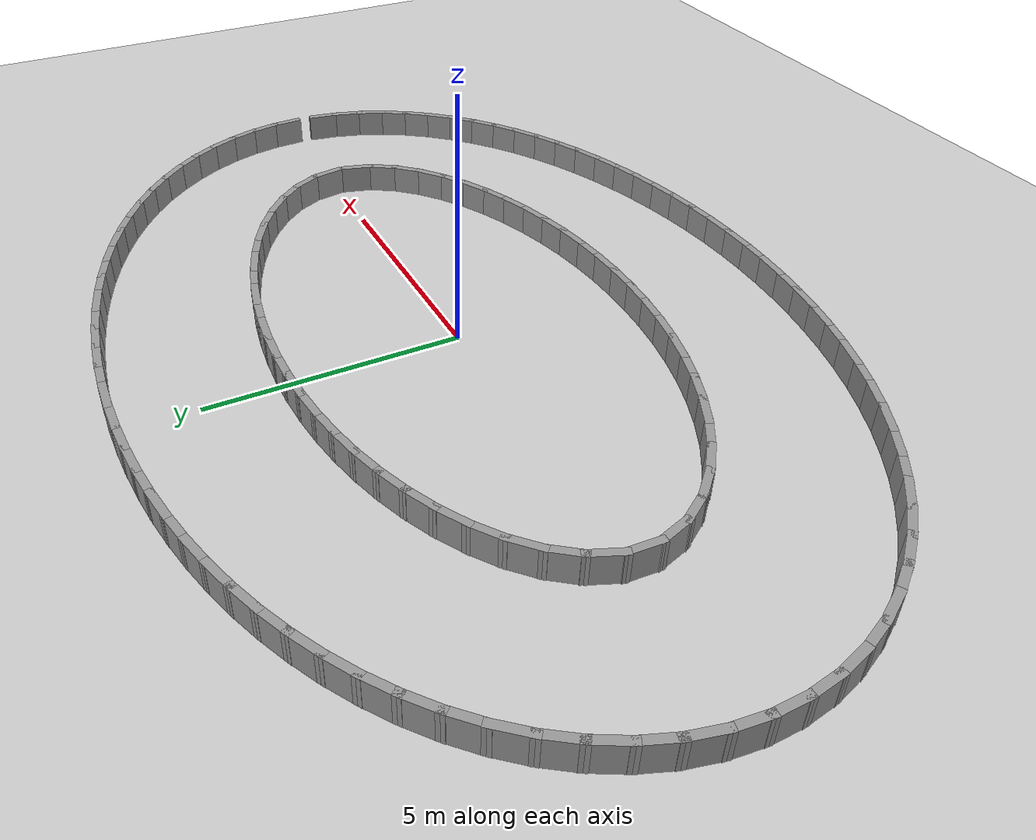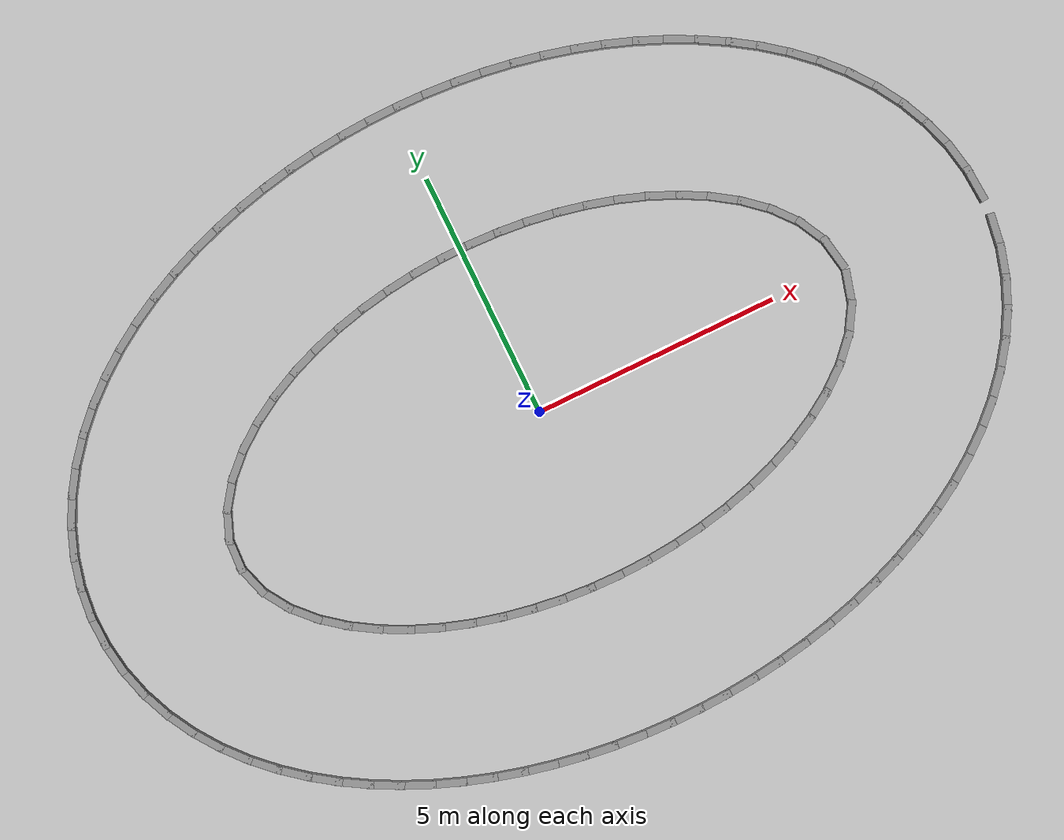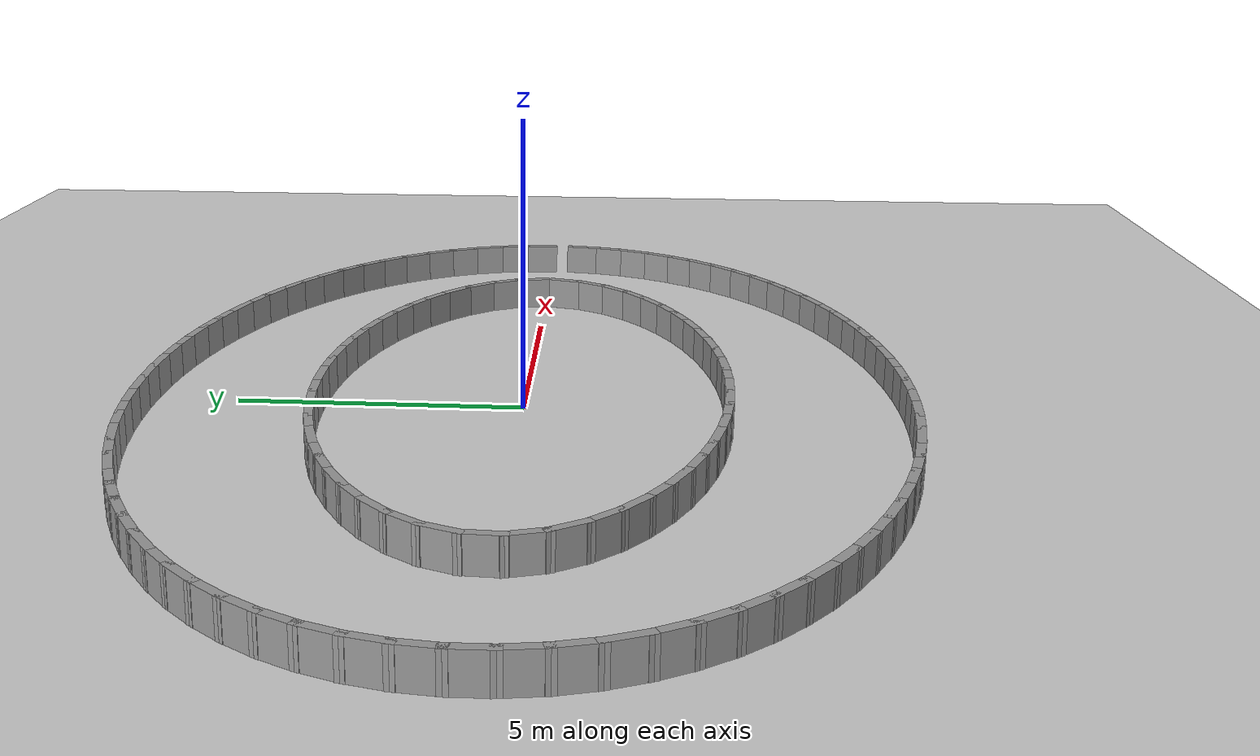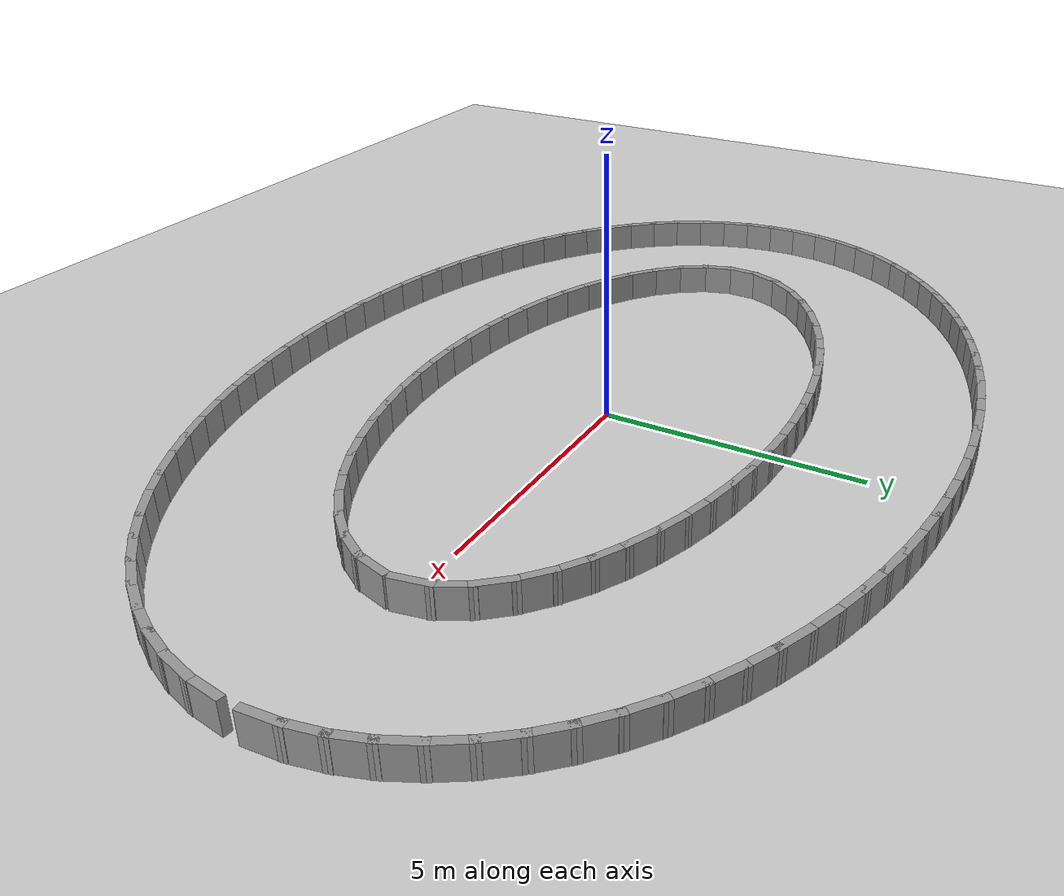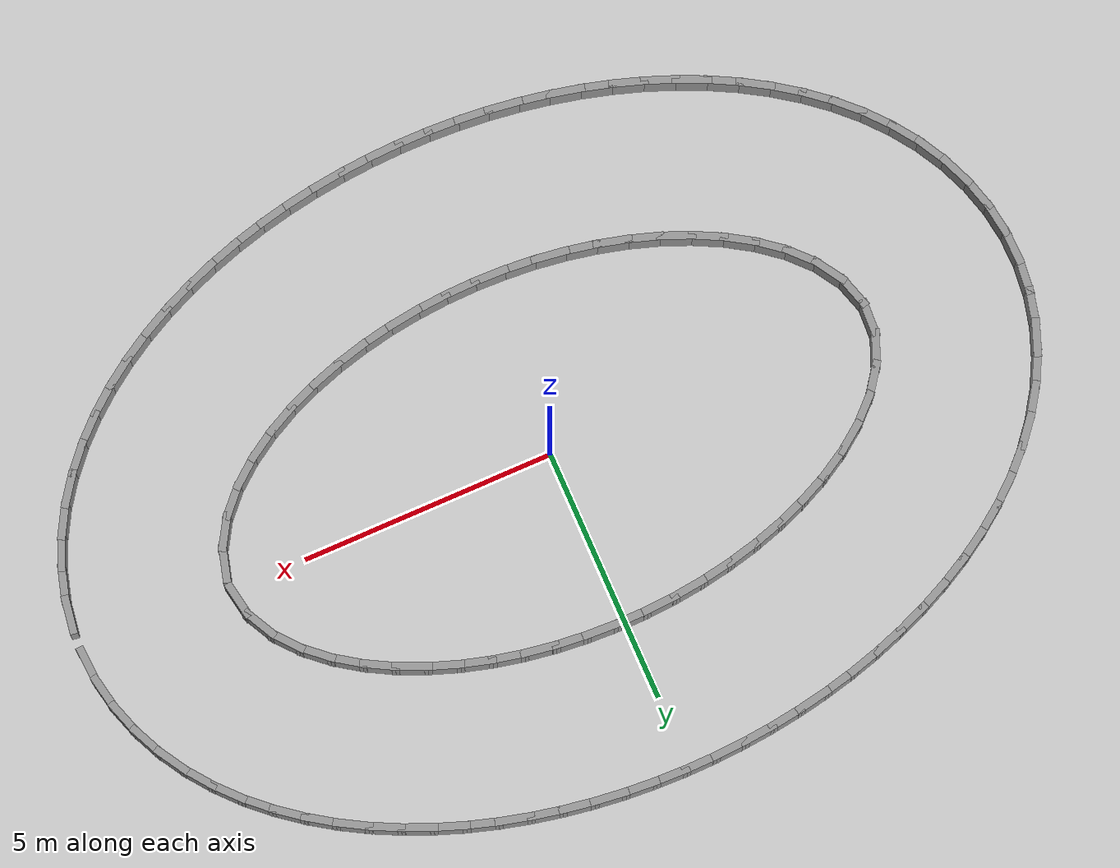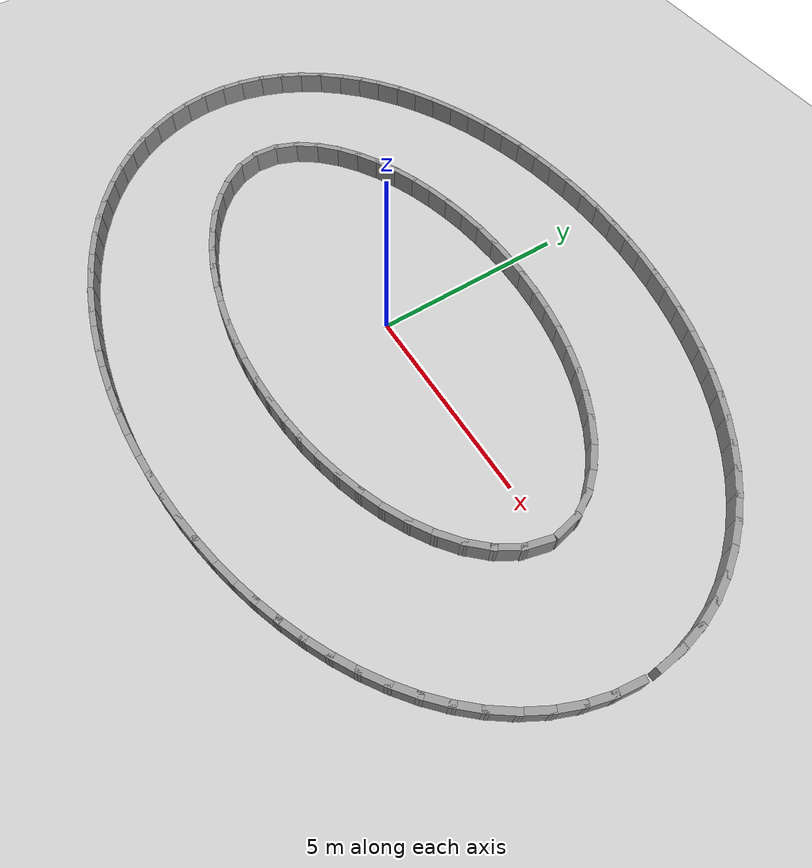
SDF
<?xml version="1.0" ?>
<sdf version='1.7'>
  <world name='default'>
    <plugin name='gazebo_ros_state' filename='libgazebo_ros_state.so'>
      <ros>
        <namespace>/</namespace>
      </ros>
      <update_rate>1000.0</update_rate>
    </plugin>

    <light name='sun' type='directional'>
      <cast_shadows>1</cast_shadows>
      <pose>0 0 10 0 -0 0</pose>
      <diffuse>0.8 0.8 0.8 1</diffuse>
      <specular>0.2 0.2 0.2 1</specular>
      <attenuation>
        <range>1000</range>
        <constant>0.9</constant>
        <linear>0.01</linear>
        <quadratic>0.001</quadratic>
      </attenuation>
      <direction>-0.5 0.1 -0.9</direction>
      <spot>
        <inner_angle>0</inner_angle>
        <outer_angle>0</outer_angle>
        <falloff>0</falloff>
      </spot>
    </light>
    <model name='ground_plane'>
      <static>1</static>
      <link name='link'>
        <collision name='collision'>
          <geometry>
            <plane>
              <normal>0 0 1</normal>
              <size>100 100</size>
            </plane>
          </geometry>
          <surface>
            <friction>
              <ode>
                <mu>100</mu>
                <mu2>50</mu2>
              </ode>
              <torsional>
                <ode/>
              </torsional>
            </friction>
            <contact>
              <ode/>
            </contact>
            <bounce/>
          </surface>
          <max_contacts>10</max_contacts>
        </collision>
        <visual name='visual'>
          <cast_shadows>0</cast_shadows>
          <geometry>
            <plane>
              <normal>0 0 1</normal>
              <size>100 100</size>
            </plane>
          </geometry>
          <material>
            <script>
              <uri>file://media/materials/scripts/gazebo.material</uri>
              <name>Gazebo/Grey</name>
            </script>
          </material>
        </visual>
        <self_collide>0</self_collide>
        <enable_wind>0</enable_wind>
        <kinematic>0</kinematic>
      </link>
    </model>
    <gravity>0 0 -9.8</gravity>
    <magnetic_field>6e-06 2.3e-05 -4.2e-05</magnetic_field>
    <atmosphere type='adiabatic'/>
    <physics type='ode'>
      <max_step_size>0.001</max_step_size>
      <real_time_factor>1</real_time_factor>
      <real_time_update_rate>1000</real_time_update_rate>
    </physics>
    <scene>
      <ambient>0.4 0.4 0.4 1</ambient>
      <background>0.7 0.7 0.7 1</background>
      <shadows>1</shadows>
    </scene>
    <audio>
      <device>default</device>
    </audio>
    <wind/>
    <spherical_coordinates>
      <surface_model>EARTH_WGS84</surface_model>
      <latitude_deg>0</latitude_deg>
      <longitude_deg>0</longitude_deg>
      <elevation>0</elevation>
      <heading_deg>0</heading_deg>
    </spherical_coordinates>
  <model name='oval_loop'>
    <pose>0 0 0 0 -0 0</pose>
    <link name='Wall_0'>
      <collision name='Wall_0_Collision'>
        <geometry><box><size>0.7470 0.1500 0.6000</size></box></geometry>
        <pose>0 0 0.3000 0 -0 0</pose>
      </collision>
      <visual name='Wall_0_Visual'>
        <pose>0 0 0.3000 0 -0 0</pose>
        <geometry><box><size>0.7470 0.1500 0.6000</size></box></geometry>
        <material>
          <script>
            <uri>file://media/materials/scripts/gazebo.material</uri>
            <name>Gazebo/Grey</name>
          </script>
          <ambient>1 1 1 1</ambient>
        </material>
      </visual>
      <pose>6.4471 0.2938 0 0 -0 1.74890</pose>
    </link>
    <link name='Wall_1'>
      <collision name='Wall_1_Collision'>
        <geometry><box><size>0.7484 0.1500 0.6000</size></box></geometry>
        <pose>0 0 0.3000 0 -0 0</pose>
      </collision>
      <visual name='Wall_1_Visual'>
        <pose>0 0 0.3000 0 -0 0</pose>
        <geometry><box><size>0.7484 0.1500 0.6000</size></box></geometry>
        <material>
          <script>
            <uri>file://media/materials/scripts/gazebo.material</uri>
            <name>Gazebo/Grey</name>
          </script>
          <ambient>1 1 1 1</ambient>
        </material>
      </visual>
      <pose>6.2561 0.8530 0 0 -0 2.05053</pose>
    </link>
    <link name='Wall_2'>
      <collision name='Wall_2_Collision'>
        <geometry><box><size>0.7492 0.1500 0.6000</size></box></geometry>
        <pose>0 0 0.3000 0 -0 0</pose>
      </collision>
      <visual name='Wall_2_Visual'>
        <pose>0 0 0.3000 0 -0 0</pose>
        <geometry><box><size>0.7492 0.1500 0.6000</size></box></geometry>
        <material>
          <script>
            <uri>file://media/materials/scripts/gazebo.material</uri>
            <name>Gazebo/Grey</name>
          </script>
          <ambient>1 1 1 1</ambient>
        </material>
      </visual>
      <pose>5.9261 1.3484 0 0 -0 2.26618</pose>
    </link>
    <link name='Wall_3'>
      <collision name='Wall_3_Collision'>
        <geometry><box><size>0.7495 0.1500 0.6000</size></box></geometry>
        <pose>0 0 0.3000 0 -0 0</pose>
      </collision>
      <visual name='Wall_3_Visual'>
        <pose>0 0 0.3000 0 -0 0</pose>
        <geometry><box><size>0.7495 0.1500 0.6000</size></box></geometry>
        <material>
          <script>
            <uri>file://media/materials/scripts/gazebo.material</uri>
            <name>Gazebo/Grey</name>
          </script>
          <ambient>1 1 1 1</ambient>
        </material>
      </visual>
      <pose>5.5084 1.7757 0 0 -0 2.42343</pose>
    </link>
    <link name='Wall_4'>
      <collision name='Wall_4_Collision'>
        <geometry><box><size>0.7497 0.1500 0.6000</size></box></geometry>
        <pose>0 0 0.3000 0 -0 0</pose>
      </collision>
      <visual name='Wall_4_Visual'>
        <pose>0 0 0.3000 0 -0 0</pose>
        <geometry><box><size>0.7497 0.1500 0.6000</size></box></geometry>
        <material>
          <script>
            <uri>file://media/materials/scripts/gazebo.material</uri>
            <name>Gazebo/Grey</name>
          </script>
          <ambient>1 1 1 1</ambient>
        </material>
      </visual>
      <pose>5.0346 2.1414 0 0 -0 2.54512</pose>
    </link>
    <link name='Wall_5'>
      <collision name='Wall_5_Collision'>
        <geometry><box><size>0.7498 0.1500 0.6000</size></box></geometry>
        <pose>0 0 0.3000 0 -0 0</pose>
      </collision>
      <visual name='Wall_5_Visual'>
        <pose>0 0 0.3000 0 -0 0</pose>
        <geometry><box><size>0.7498 0.1500 0.6000</size></box></geometry>
        <material>
          <script>
            <uri>file://media/materials/scripts/gazebo.material</uri>
            <name>Gazebo/Grey</name>
          </script>
          <ambient>1 1 1 1</ambient>
        </material>
      </visual>
      <pose>4.5230 2.4529 0 0 -0 2.64436</pose>
    </link>
    <link name='Wall_6'>
      <collision name='Wall_6_Collision'>
        <geometry><box><size>0.7498 0.1500 0.6000</size></box></geometry>
        <pose>0 0 0.3000 0 -0 0</pose>
      </collision>
      <visual name='Wall_6_Visual'>
        <pose>0 0 0.3000 0 -0 0</pose>
        <geometry><box><size>0.7498 0.1500 0.6000</size></box></geometry>
        <material>
          <script>
            <uri>file://media/materials/scripts/gazebo.material</uri>
            <name>Gazebo/Grey</name>
          </script>
          <ambient>1 1 1 1</ambient>
        </material>
      </visual>
      <pose>3.9847 2.7163 0 0 -0 2.72867</pose>
    </link>
    <link name='Wall_7'>
      <collision name='Wall_7_Collision'>
        <geometry><box><size>0.7499 0.1500 0.6000</size></box></geometry>
        <pose>0 0 0.3000 0 -0 0</pose>
      </collision>
      <visual name='Wall_7_Visual'>
        <pose>0 0 0.3000 0 -0 0</pose>
        <geometry><box><size>0.7499 0.1500 0.6000</size></box></geometry>
        <material>
          <script>
            <uri>file://media/materials/scripts/gazebo.material</uri>
            <name>Gazebo/Grey</name>
          </script>
          <ambient>1 1 1 1</ambient>
        </material>
      </visual>
      <pose>3.4271 2.9363 0 0 -0 2.80269</pose>
    </link>
    <link name='Wall_8'>
      <collision name='Wall_8_Collision'>
        <geometry><box><size>0.7499 0.1500 0.6000</size></box></geometry>
        <pose>0 0 0.3000 0 -0 0</pose>
      </collision>
      <visual name='Wall_8_Visual'>
        <pose>0 0 0.3000 0 -0 0</pose>
        <geometry><box><size>0.7499 0.1500 0.6000</size></box></geometry>
        <material>
          <script>
            <uri>file://media/materials/scripts/gazebo.material</uri>
            <name>Gazebo/Grey</name>
          </script>
          <ambient>1 1 1 1</ambient>
        </material>
      </visual>
      <pose>2.8553 3.1167 0 0 -0 2.86947</pose>
    </link>
    <link name='Wall_9'>
      <collision name='Wall_9_Collision'>
        <geometry><box><size>0.7499 0.1500 0.6000</size></box></geometry>
        <pose>0 0 0.3000 0 -0 0</pose>
      </collision>
      <visual name='Wall_9_Visual'>
        <pose>0 0 0.3000 0 -0 0</pose>
        <geometry><box><size>0.7499 0.1500 0.6000</size></box></geometry>
        <material>
          <script>
            <uri>file://media/materials/scripts/gazebo.material</uri>
            <name>Gazebo/Grey</name>
          </script>
          <ambient>1 1 1 1</ambient>
        </material>
      </visual>
      <pose>2.2731 3.2600 0 0 -0 2.93099</pose>
    </link>
    <link name='Wall_10'>
      <collision name='Wall_10_Collision'>
        <geometry><box><size>0.7499 0.1500 0.6000</size></box></geometry>
        <pose>0 0 0.3000 0 -0 0</pose>
      </collision>
      <visual name='Wall_10_Visual'>
        <pose>0 0 0.3000 0 -0 0</pose>
        <geometry><box><size>0.7499 0.1500 0.6000</size></box></geometry>
        <material>
          <script>
            <uri>file://media/materials/scripts/gazebo.material</uri>
            <name>Gazebo/Grey</name>
          </script>
          <ambient>1 1 1 1</ambient>
        </material>
      </visual>
      <pose>1.6833 3.3683 0 0 -0 2.98885</pose>
    </link>
    <link name='Wall_11'>
      <collision name='Wall_11_Collision'>
        <geometry><box><size>0.7499 0.1500 0.6000</size></box></geometry>
        <pose>0 0 0.3000 0 -0 0</pose>
      </collision>
      <visual name='Wall_11_Visual'>
        <pose>0 0 0.3000 0 -0 0</pose>
        <geometry><box><size>0.7499 0.1500 0.6000</size></box></geometry>
        <material>
          <script>
            <uri>file://media/materials/scripts/gazebo.material</uri>
            <name>Gazebo/Grey</name>
          </script>
          <ambient>1 1 1 1</ambient>
        </material>
      </visual>
      <pose>1.0883 3.4431 0 0 -0 3.04424</pose>
    </link>
    <link name='Wall_12'>
      <collision name='Wall_12_Collision'>
        <geometry><box><size>0.7499 0.1500 0.6000</size></box></geometry>
        <pose>0 0 0.3000 0 -0 0</pose>
      </collision>
      <visual name='Wall_12_Visual'>
        <pose>0 0 0.3000 0 -0 0</pose>
        <geometry><box><size>0.7499 0.1500 0.6000</size></box></geometry>
        <material>
          <script>
            <uri>file://media/materials/scripts/gazebo.material</uri>
            <name>Gazebo/Grey</name>
          </script>
          <ambient>1 1 1 1</ambient>
        </material>
      </visual>
      <pose>0.4900 3.4853 0 0 -0 3.09809</pose>
    </link>
    <link name='Wall_13'>
      <collision name='Wall_13_Collision'>
        <geometry><box><size>0.7499 0.1500 0.6000</size></box></geometry>
        <pose>0 0 0.3000 0 -0 0</pose>
      </collision>
      <visual name='Wall_13_Visual'>
        <pose>0 0 0.3000 0 -0 0</pose>
        <geometry><box><size>0.7499 0.1500 0.6000</size></box></geometry>
        <material>
          <script>
            <uri>file://media/materials/scripts/gazebo.material</uri>
            <name>Gazebo/Grey</name>
          </script>
          <ambient>1 1 1 1</ambient>
        </material>
      </visual>
      <pose>-0.1096 3.4955 0 0 -0 -3.13189</pose>
    </link>
    <link name='Wall_14'>
      <collision name='Wall_14_Collision'>
        <geometry><box><size>0.7499 0.1500 0.6000</size></box></geometry>
        <pose>0 0 0.3000 0 -0 0</pose>
      </collision>
      <visual name='Wall_14_Visual'>
        <pose>0 0 0.3000 0 -0 0</pose>
        <geometry><box><size>0.7499 0.1500 0.6000</size></box></geometry>
        <material>
          <script>
            <uri>file://media/materials/scripts/gazebo.material</uri>
            <name>Gazebo/Grey</name>
          </script>
          <ambient>1 1 1 1</ambient>
        </material>
      </visual>
      <pose>-0.7089 3.4737 0 0 -0 -3.07852</pose>
    </link>
    <link name='Wall_15'>
      <collision name='Wall_15_Collision'>
        <geometry><box><size>0.7499 0.1500 0.6000</size></box></geometry>
        <pose>0 0 0.3000 0 -0 0</pose>
      </collision>
      <visual name='Wall_15_Visual'>
        <pose>0 0 0.3000 0 -0 0</pose>
        <geometry><box><size>0.7499 0.1500 0.6000</size></box></geometry>
        <material>
          <script>
            <uri>file://media/materials/scripts/gazebo.material</uri>
            <name>Gazebo/Grey</name>
          </script>
          <ambient>1 1 1 1</ambient>
        </material>
      </visual>
      <pose>-1.3062 3.4196 0 0 -0 -3.02423</pose>
    </link>
    <link name='Wall_16'>
      <collision name='Wall_16_Collision'>
        <geometry><box><size>0.7499 0.1500 0.6000</size></box></geometry>
        <pose>0 0 0.3000 0 -0 0</pose>
      </collision>
      <visual name='Wall_16_Visual'>
        <pose>0 0 0.3000 0 -0 0</pose>
        <geometry><box><size>0.7499 0.1500 0.6000</size></box></geometry>
        <material>
          <script>
            <uri>file://media/materials/scripts/gazebo.material</uri>
            <name>Gazebo/Grey</name>
          </script>
          <ambient>1 1 1 1</ambient>
        </material>
      </visual>
      <pose>-1.8995 3.3327 0 0 -0 -2.96804</pose>
    </link>
    <link name='Wall_17'>
      <collision name='Wall_17_Collision'>
        <geometry><box><size>0.7499 0.1500 0.6000</size></box></geometry>
        <pose>0 0 0.3000 0 -0 0</pose>
      </collision>
      <visual name='Wall_17_Visual'>
        <pose>0 0 0.3000 0 -0 0</pose>
        <geometry><box><size>0.7499 0.1500 0.6000</size></box></geometry>
        <material>
          <script>
            <uri>file://media/materials/scripts/gazebo.material</uri>
            <name>Gazebo/Grey</name>
          </script>
          <ambient>1 1 1 1</ambient>
        </material>
      </visual>
      <pose>-2.4869 3.2118 0 0 -0 -2.90900</pose>
    </link>
    <link name='Wall_18'>
      <collision name='Wall_18_Collision'>
        <geometry><box><size>0.7499 0.1500 0.6000</size></box></geometry>
        <pose>0 0 0.3000 0 -0 0</pose>
      </collision>
      <visual name='Wall_18_Visual'>
        <pose>0 0 0.3000 0 -0 0</pose>
        <geometry><box><size>0.7499 0.1500 0.6000</size></box></geometry>
        <material>
          <script>
            <uri>file://media/materials/scripts/gazebo.material</uri>
            <name>Gazebo/Grey</name>
          </script>
          <ambient>1 1 1 1</ambient>
        </material>
      </visual>
      <pose>-3.0656 3.0552 0 0 -0 -2.84574</pose>
    </link>
    <link name='Wall_19'>
      <collision name='Wall_19_Collision'>
        <geometry><box><size>0.7499 0.1500 0.6000</size></box></geometry>
        <pose>0 0 0.3000 0 -0 0</pose>
      </collision>
      <visual name='Wall_19_Visual'>
        <pose>0 0 0.3000 0 -0 0</pose>
        <geometry><box><size>0.7499 0.1500 0.6000</size></box></geometry>
        <material>
          <script>
            <uri>file://media/materials/scripts/gazebo.material</uri>
            <name>Gazebo/Grey</name>
          </script>
          <ambient>1 1 1 1</ambient>
        </material>
      </visual>
      <pose>-3.6327 2.8607 0 0 -0 -2.77665</pose>
    </link>
    <link name='Wall_20'>
      <collision name='Wall_20_Collision'>
        <geometry><box><size>0.7498 0.1500 0.6000</size></box></geometry>
        <pose>0 0 0.3000 0 -0 0</pose>
      </collision>
      <visual name='Wall_20_Visual'>
        <pose>0 0 0.3000 0 -0 0</pose>
        <geometry><box><size>0.7498 0.1500 0.6000</size></box></geometry>
        <material>
          <script>
            <uri>file://media/materials/scripts/gazebo.material</uri>
            <name>Gazebo/Grey</name>
          </script>
          <ambient>1 1 1 1</ambient>
        </material>
      </visual>
      <pose>-4.1840 2.6253 0 0 -0 -2.69924</pose>
    </link>
    <link name='Wall_21'>
      <collision name='Wall_21_Collision'>
        <geometry><box><size>0.7498 0.1500 0.6000</size></box></geometry>
        <pose>0 0 0.3000 0 -0 0</pose>
      </collision>
      <visual name='Wall_21_Visual'>
        <pose>0 0 0.3000 0 -0 0</pose>
        <geometry><box><size>0.7498 0.1500 0.6000</size></box></geometry>
        <material>
          <script>
            <uri>file://media/materials/scripts/gazebo.material</uri>
            <name>Gazebo/Grey</name>
          </script>
          <ambient>1 1 1 1</ambient>
        </material>
      </visual>
      <pose>-4.7135 2.3449 0 0 -0 -2.61013</pose>
    </link>
    <link name='Wall_22'>
      <collision name='Wall_22_Collision'>
        <geometry><box><size>0.7497 0.1500 0.6000</size></box></geometry>
        <pose>0 0 0.3000 0 -0 0</pose>
      </collision>
      <visual name='Wall_22_Visual'>
        <pose>0 0 0.3000 0 -0 0</pose>
        <geometry><box><size>0.7497 0.1500 0.6000</size></box></geometry>
        <material>
          <script>
            <uri>file://media/materials/scripts/gazebo.material</uri>
            <name>Gazebo/Grey</name>
          </script>
          <ambient>1 1 1 1</ambient>
        </material>
      </visual>
      <pose>-5.2129 2.0144 0 0 -0 -2.50378</pose>
    </link>
    <link name='Wall_23'>
      <collision name='Wall_23_Collision'>
        <geometry><box><size>0.7494 0.1500 0.6000</size></box></geometry>
        <pose>0 0 0.3000 0 -0 0</pose>
      </collision>
      <visual name='Wall_23_Visual'>
        <pose>0 0 0.3000 0 -0 0</pose>
        <geometry><box><size>0.7494 0.1500 0.6000</size></box></geometry>
        <material>
          <script>
            <uri>file://media/materials/scripts/gazebo.material</uri>
            <name>Gazebo/Grey</name>
          </script>
          <ambient>1 1 1 1</ambient>
        </material>
      </visual>
      <pose>-5.6689 1.6271 0 0 -0 -2.37104</pose>
    </link>
    <link name='Wall_24'>
      <collision name='Wall_24_Collision'>
        <geometry><box><size>0.7490 0.1500 0.6000</size></box></geometry>
        <pose>0 0 0.3000 0 -0 0</pose>
      </collision>
      <visual name='Wall_24_Visual'>
        <pose>0 0 0.3000 0 -0 0</pose>
        <geometry><box><size>0.7490 0.1500 0.6000</size></box></geometry>
        <material>
          <script>
            <uri>file://media/materials/scripts/gazebo.material</uri>
            <name>Gazebo/Grey</name>
          </script>
          <ambient>1 1 1 1</ambient>
        </material>
      </visual>
      <pose>-6.0591 1.1755 0 0 -0 -2.19573</pose>
    </link>
    <link name='Wall_25'>
      <collision name='Wall_25_Collision'>
        <geometry><box><size>0.7479 0.1500 0.6000</size></box></geometry>
        <pose>0 0 0.3000 0 -0 0</pose>
      </collision>
      <visual name='Wall_25_Visual'>
        <pose>0 0 0.3000 0 -0 0</pose>
        <geometry><box><size>0.7479 0.1500 0.6000</size></box></geometry>
        <material>
          <script>
            <uri>file://media/materials/scripts/gazebo.material</uri>
            <name>Gazebo/Grey</name>
          </script>
          <ambient>1 1 1 1</ambient>
        </material>
      </visual>
      <pose>-6.3453 0.6550 0 0 -0 -1.95104</pose>
    </link>
    <link name='Wall_26'>
      <collision name='Wall_26_Collision'>
        <geometry><box><size>0.7467 0.1500 0.6000</size></box></geometry>
        <pose>0 0 0.3000 0 -0 0</pose>
      </collision>
      <visual name='Wall_26_Visual'>
        <pose>0 0 0.3000 0 -0 0</pose>
        <geometry><box><size>0.7467 0.1500 0.6000</size></box></geometry>
        <material>
          <script>
            <uri>file://media/materials/scripts/gazebo.material</uri>
            <name>Gazebo/Grey</name>
          </script>
          <ambient>1 1 1 1</ambient>
        </material>
      </visual>
      <pose>-6.4708 0.0794 0 0 -0 -1.61950</pose>
    </link>
    <link name='Wall_27'>
      <collision name='Wall_27_Collision'>
        <geometry><box><size>0.7475 0.1500 0.6000</size></box></geometry>
        <pose>0 0 0.3000 0 -0 0</pose>
      </collision>
      <visual name='Wall_27_Visual'>
        <pose>0 0 0.3000 0 -0 0</pose>
        <geometry><box><size>0.7475 0.1500 0.6000</size></box></geometry>
        <material>
          <script>
            <uri>file://media/materials/scripts/gazebo.material</uri>
            <name>Gazebo/Grey</name>
          </script>
          <ambient>1 1 1 1</ambient>
        </material>
      </visual>
      <pose>-6.3973 -0.5041 0 0 -0 -1.27190</pose>
    </link>
    <link name='Wall_28'>
      <collision name='Wall_28_Collision'>
        <geometry><box><size>0.7487 0.1500 0.6000</size></box></geometry>
        <pose>0 0 0.3000 0 -0 0</pose>
      </collision>
      <visual name='Wall_28_Visual'>
        <pose>0 0 0.3000 0 -0 0</pose>
        <geometry><box><size>0.7487 0.1500 0.6000</size></box></geometry>
        <material>
          <script>
            <uri>file://media/materials/scripts/gazebo.material</uri>
            <name>Gazebo/Grey</name>
          </script>
          <ambient>1 1 1 1</ambient>
        </material>
      </visual>
      <pose>-6.1485 -1.0421 0 0 -0 -1.00353</pose>
    </link>
    <link name='Wall_29'>
      <collision name='Wall_29_Collision'>
        <geometry><box><size>0.7493 0.1500 0.6000</size></box></geometry>
        <pose>0 0 0.3000 0 -0 0</pose>
      </collision>
      <visual name='Wall_29_Visual'>
        <pose>0 0 0.3000 0 -0 0</pose>
        <geometry><box><size>0.7493 0.1500 0.6000</size></box></geometry>
        <material>
          <script>
            <uri>file://media/materials/scripts/gazebo.material</uri>
            <name>Gazebo/Grey</name>
          </script>
          <ambient>1 1 1 1</ambient>
        </material>
      </visual>
      <pose>-5.7816 -1.5122 0 0 -0 -0.81263</pose>
    </link>
    <link name='Wall_30'>
      <collision name='Wall_30_Collision'>
        <geometry><box><size>0.7496 0.1500 0.6000</size></box></geometry>
        <pose>0 0 0.3000 0 -0 0</pose>
      </collision>
      <visual name='Wall_30_Visual'>
        <pose>0 0 0.3000 0 -0 0</pose>
        <geometry><box><size>0.7496 0.1500 0.6000</size></box></geometry>
        <material>
          <script>
            <uri>file://media/materials/scripts/gazebo.material</uri>
            <name>Gazebo/Grey</name>
          </script>
          <ambient>1 1 1 1</ambient>
        </material>
      </visual>
      <pose>-5.3406 -1.9161 0 0 -0 -0.67044</pose>
    </link>
    <link name='Wall_31'>
      <collision name='Wall_31_Collision'>
        <geometry><box><size>0.7497 0.1500 0.6000</size></box></geometry>
        <pose>0 0 0.3000 0 -0 0</pose>
      </collision>
      <visual name='Wall_31_Visual'>
        <pose>0 0 0.3000 0 -0 0</pose>
        <geometry><box><size>0.7497 0.1500 0.6000</size></box></geometry>
        <material>
          <script>
            <uri>file://media/materials/scripts/gazebo.material</uri>
            <name>Gazebo/Grey</name>
          </script>
          <ambient>1 1 1 1</ambient>
        </material>
      </visual>
      <pose>-4.8513 -2.2611 0 0 -0 -0.55810</pose>
    </link>
    <link name='Wall_32'>
      <collision name='Wall_32_Collision'>
        <geometry><box><size>0.7498 0.1500 0.6000</size></box></geometry>
        <pose>0 0 0.3000 0 -0 0</pose>
      </collision>
      <visual name='Wall_32_Visual'>
        <pose>0 0 0.3000 0 -0 0</pose>
        <geometry><box><size>0.7498 0.1500 0.6000</size></box></geometry>
        <material>
          <script>
            <uri>file://media/materials/scripts/gazebo.material</uri>
            <name>Gazebo/Grey</name>
          </script>
          <ambient>1 1 1 1</ambient>
        </material>
      </visual>
      <pose>-4.3289 -2.5544 0 0 -0 -0.46498</pose>
    </link>
    <link name='Wall_33'>
      <collision name='Wall_33_Collision'>
        <geometry><box><size>0.7499 0.1500 0.6000</size></box></geometry>
        <pose>0 0 0.3000 0 -0 0</pose>
      </collision>
      <visual name='Wall_33_Visual'>
        <pose>0 0 0.3000 0 -0 0</pose>
        <geometry><box><size>0.7499 0.1500 0.6000</size></box></geometry>
        <material>
          <script>
            <uri>file://media/materials/scripts/gazebo.material</uri>
            <name>Gazebo/Grey</name>
          </script>
          <ambient>1 1 1 1</ambient>
        </material>
      </visual>
      <pose>-3.7828 -2.8015 0 0 -0 -0.38485</pose>
    </link>
    <link name='Wall_34'>
      <collision name='Wall_34_Collision'>
        <geometry><box><size>0.7499 0.1500 0.6000</size></box></geometry>
        <pose>0 0 0.3000 0 -0 0</pose>
      </collision>
      <visual name='Wall_34_Visual'>
        <pose>0 0 0.3000 0 -0 0</pose>
        <geometry><box><size>0.7499 0.1500 0.6000</size></box></geometry>
        <material>
          <script>
            <uri>file://media/materials/scripts/gazebo.material</uri>
            <name>Gazebo/Grey</name>
          </script>
          <ambient>1 1 1 1</ambient>
        </material>
      </visual>
      <pose>-3.2196 -3.0067 0 0 -0 -0.31378</pose>
    </link>
    <link name='Wall_35'>
      <collision name='Wall_35_Collision'>
        <geometry><box><size>0.7499 0.1500 0.6000</size></box></geometry>
        <pose>0 0 0.3000 0 -0 0</pose>
      </collision>
      <visual name='Wall_35_Visual'>
        <pose>0 0 0.3000 0 -0 0</pose>
        <geometry><box><size>0.7499 0.1500 0.6000</size></box></geometry>
        <material>
          <script>
            <uri>file://media/materials/scripts/gazebo.material</uri>
            <name>Gazebo/Grey</name>
          </script>
          <ambient>1 1 1 1</ambient>
        </material>
      </visual>
      <pose>-2.6436 -3.1732 0 0 -0 -0.24916</pose>
    </link>
    <link name='Wall_36'>
      <collision name='Wall_36_Collision'>
        <geometry><box><size>0.7499 0.1500 0.6000</size></box></geometry>
        <pose>0 0 0.3000 0 -0 0</pose>
      </collision>
      <visual name='Wall_36_Visual'>
        <pose>0 0 0.3000 0 -0 0</pose>
        <geometry><box><size>0.7499 0.1500 0.6000</size></box></geometry>
        <material>
          <script>
            <uri>file://media/materials/scripts/gazebo.material</uri>
            <name>Gazebo/Grey</name>
          </script>
          <ambient>1 1 1 1</ambient>
        </material>
      </visual>
      <pose>-2.0583 -3.3036 0 0 -0 -0.18909</pose>
    </link>
    <link name='Wall_37'>
      <collision name='Wall_37_Collision'>
        <geometry><box><size>0.7499 0.1500 0.6000</size></box></geometry>
        <pose>0 0 0.3000 0 -0 0</pose>
      </collision>
      <visual name='Wall_37_Visual'>
        <pose>0 0 0.3000 0 -0 0</pose>
        <geometry><box><size>0.7499 0.1500 0.6000</size></box></geometry>
        <material>
          <script>
            <uri>file://media/materials/scripts/gazebo.material</uri>
            <name>Gazebo/Grey</name>
          </script>
          <ambient>1 1 1 1</ambient>
        </material>
      </visual>
      <pose>-1.4663 -3.3995 0 0 -0 -0.13227</pose>
    </link>
    <link name='Wall_38'>
      <collision name='Wall_38_Collision'>
        <geometry><box><size>0.7499 0.1500 0.6000</size></box></geometry>
        <pose>0 0 0.3000 0 -0 0</pose>
      </collision>
      <visual name='Wall_38_Visual'>
        <pose>0 0 0.3000 0 -0 0</pose>
        <geometry><box><size>0.7499 0.1500 0.6000</size></box></geometry>
        <material>
          <script>
            <uri>file://media/materials/scripts/gazebo.material</uri>
            <name>Gazebo/Grey</name>
          </script>
          <ambient>1 1 1 1</ambient>
        </material>
      </visual>
      <pose>-0.8699 -3.4623 0 0 -0 -0.07754</pose>
    </link>
    <link name='Wall_39'>
      <collision name='Wall_39_Collision'>
        <geometry><box><size>0.7499 0.1500 0.6000</size></box></geometry>
        <pose>0 0 0.3000 0 -0 0</pose>
      </collision>
      <visual name='Wall_39_Visual'>
        <pose>0 0 0.3000 0 -0 0</pose>
        <geometry><box><size>0.7499 0.1500 0.6000</size></box></geometry>
        <material>
          <script>
            <uri>file://media/materials/scripts/gazebo.material</uri>
            <name>Gazebo/Grey</name>
          </script>
          <ambient>1 1 1 1</ambient>
        </material>
      </visual>
      <pose>-0.2710 -3.4927 0 0 -0 -0.02403</pose>
    </link>
    <link name='Wall_40'>
      <collision name='Wall_40_Collision'>
        <geometry><box><size>0.7499 0.1500 0.6000</size></box></geometry>
        <pose>0 0 0.3000 0 -0 0</pose>
      </collision>
      <visual name='Wall_40_Visual'>
        <pose>0 0 0.3000 0 -0 0</pose>
        <geometry><box><size>0.7499 0.1500 0.6000</size></box></geometry>
        <material>
          <script>
            <uri>file://media/materials/scripts/gazebo.material</uri>
            <name>Gazebo/Grey</name>
          </script>
          <ambient>1 1 1 1</ambient>
        </material>
      </visual>
      <pose>0.3287 -3.4912 0 0 -0 0.02913</pose>
    </link>
    <link name='Wall_41'>
      <collision name='Wall_41_Collision'>
        <geometry><box><size>0.7499 0.1500 0.6000</size></box></geometry>
        <pose>0 0 0.3000 0 -0 0</pose>
      </collision>
      <visual name='Wall_41_Visual'>
        <pose>0 0 0.3000 0 -0 0</pose>
        <geometry><box><size>0.7499 0.1500 0.6000</size></box></geometry>
        <material>
          <script>
            <uri>file://media/materials/scripts/gazebo.material</uri>
            <name>Gazebo/Grey</name>
          </script>
          <ambient>1 1 1 1</ambient>
        </material>
      </visual>
      <pose>0.9275 -3.4577 0 0 -0 0.08277</pose>
    </link>
    <link name='Wall_42'>
      <collision name='Wall_42_Collision'>
        <geometry><box><size>0.7499 0.1500 0.6000</size></box></geometry>
        <pose>0 0 0.3000 0 -0 0</pose>
      </collision>
      <visual name='Wall_42_Visual'>
        <pose>0 0 0.3000 0 -0 0</pose>
        <geometry><box><size>0.7499 0.1500 0.6000</size></box></geometry>
        <material>
          <script>
            <uri>file://media/materials/scripts/gazebo.material</uri>
            <name>Gazebo/Grey</name>
          </script>
          <ambient>1 1 1 1</ambient>
        </material>
      </visual>
      <pose>1.5236 -3.3917 0 0 -0 0.13762</pose>
    </link>
    <link name='Wall_43'>
      <collision name='Wall_43_Collision'>
        <geometry><box><size>0.7499 0.1500 0.6000</size></box></geometry>
        <pose>0 0 0.3000 0 -0 0</pose>
      </collision>
      <visual name='Wall_43_Visual'>
        <pose>0 0 0.3000 0 -0 0</pose>
        <geometry><box><size>0.7499 0.1500 0.6000</size></box></geometry>
        <material>
          <script>
            <uri>file://media/materials/scripts/gazebo.material</uri>
            <name>Gazebo/Grey</name>
          </script>
          <ambient>1 1 1 1</ambient>
        </material>
      </visual>
      <pose>2.1150 -3.2925 0 0 -0 0.19473</pose>
    </link>
    <link name='Wall_44'>
      <collision name='Wall_44_Collision'>
        <geometry><box><size>0.7499 0.1500 0.6000</size></box></geometry>
        <pose>0 0 0.3000 0 -0 0</pose>
      </collision>
      <visual name='Wall_44_Visual'>
        <pose>0 0 0.3000 0 -0 0</pose>
        <geometry><box><size>0.7499 0.1500 0.6000</size></box></geometry>
        <material>
          <script>
            <uri>file://media/materials/scripts/gazebo.material</uri>
            <name>Gazebo/Grey</name>
          </script>
          <ambient>1 1 1 1</ambient>
        </material>
      </visual>
      <pose>2.6995 -3.1588 0 0 -0 0.25515</pose>
    </link>
    <link name='Wall_45'>
      <collision name='Wall_45_Collision'>
        <geometry><box><size>0.7499 0.1500 0.6000</size></box></geometry>
        <pose>0 0 0.3000 0 -0 0</pose>
      </collision>
      <visual name='Wall_45_Visual'>
        <pose>0 0 0.3000 0 -0 0</pose>
        <geometry><box><size>0.7499 0.1500 0.6000</size></box></geometry>
        <material>
          <script>
            <uri>file://media/materials/scripts/gazebo.material</uri>
            <name>Gazebo/Grey</name>
          </script>
          <ambient>1 1 1 1</ambient>
        </material>
      </visual>
      <pose>3.2744 -2.9886 0 0 -0 0.32031</pose>
    </link>
    <link name='Wall_46'>
      <collision name='Wall_46_Collision'>
        <geometry><box><size>0.7499 0.1500 0.6000</size></box></geometry>
        <pose>0 0 0.3000 0 -0 0</pose>
      </collision>
      <visual name='Wall_46_Visual'>
        <pose>0 0 0.3000 0 -0 0</pose>
        <geometry><box><size>0.7499 0.1500 0.6000</size></box></geometry>
        <material>
          <script>
            <uri>file://media/materials/scripts/gazebo.material</uri>
            <name>Gazebo/Grey</name>
          </script>
          <ambient>1 1 1 1</ambient>
        </material>
      </visual>
      <pose>3.8363 -2.7796 0 0 -0 0.39212</pose>
    </link>
    <link name='Wall_47'>
      <collision name='Wall_47_Collision'>
        <geometry><box><size>0.7498 0.1500 0.6000</size></box></geometry>
        <pose>0 0 0.3000 0 -0 0</pose>
      </collision>
      <visual name='Wall_47_Visual'>
        <pose>0 0 0.3000 0 -0 0</pose>
        <geometry><box><size>0.7498 0.1500 0.6000</size></box></geometry>
        <material>
          <script>
            <uri>file://media/materials/scripts/gazebo.material</uri>
            <name>Gazebo/Grey</name>
          </script>
          <ambient>1 1 1 1</ambient>
        </material>
      </visual>
      <pose>4.3804 -2.5283 0 0 -0 0.47332</pose>
    </link>
    <link name='Wall_48'>
      <collision name='Wall_48_Collision'>
        <geometry><box><size>0.7497 0.1500 0.6000</size></box></geometry>
        <pose>0 0 0.3000 0 -0 0</pose>
      </collision>
      <visual name='Wall_48_Visual'>
        <pose>0 0 0.3000 0 -0 0</pose>
        <geometry><box><size>0.7497 0.1500 0.6000</size></box></geometry>
        <material>
          <script>
            <uri>file://media/materials/scripts/gazebo.material</uri>
            <name>Gazebo/Grey</name>
          </script>
          <ambient>1 1 1 1</ambient>
        </material>
      </visual>
      <pose>4.9001 -2.2302 0 0 -0 0.56794</pose>
    </link>
    <link name='Wall_49'>
      <collision name='Wall_49_Collision'>
        <geometry><box><size>0.7496 0.1500 0.6000</size></box></geometry>
        <pose>0 0 0.3000 0 -0 0</pose>
      </collision>
      <visual name='Wall_49_Visual'>
        <pose>0 0 0.3000 0 -0 0</pose>
        <geometry><box><size>0.7496 0.1500 0.6000</size></box></geometry>
        <material>
          <script>
            <uri>file://media/materials/scripts/gazebo.material</uri>
            <name>Gazebo/Grey</name>
          </script>
          <ambient>1 1 1 1</ambient>
        </material>
      </visual>
      <pose>5.3855 -1.8798 0 0 -0 0.68260</pose>
    </link>
    <link name='Wall_50'>
      <collision name='Wall_50_Collision'>
        <geometry><box><size>0.7493 0.1500 0.6000</size></box></geometry>
        <pose>0 0 0.3000 0 -0 0</pose>
      </collision>
      <visual name='Wall_50_Visual'>
        <pose>0 0 0.3000 0 -0 0</pose>
        <geometry><box><size>0.7493 0.1500 0.6000</size></box></geometry>
        <material>
          <script>
            <uri>file://media/materials/scripts/gazebo.material</uri>
            <name>Gazebo/Grey</name>
          </script>
          <ambient>1 1 1 1</ambient>
        </material>
      </visual>
      <pose>5.8207 -1.4699 0 0 -0 0.82854</pose>
    </link>
    <link name='Wall_51'>
      <collision name='Wall_51_Collision'>
        <geometry><box><size>0.7487 0.1500 0.6000</size></box></geometry>
        <pose>0 0 0.3000 0 -0 0</pose>
      </collision>
      <visual name='Wall_51_Visual'>
        <pose>0 0 0.3000 0 -0 0</pose>
        <geometry><box><size>0.7487 0.1500 0.6000</size></box></geometry>
        <material>
          <script>
            <uri>file://media/materials/scripts/gazebo.material</uri>
            <name>Gazebo/Grey</name>
          </script>
          <ambient>1 1 1 1</ambient>
        </material>
      </visual>
      <pose>6.1785 -0.9931 0 0 -0 1.02552</pose>
    </link>
    <link name='Wall_52'>
      <collision name='Wall_52_Collision'>
        <geometry><box><size>0.7474 0.1500 0.6000</size></box></geometry>
        <pose>0 0 0.3000 0 -0 0</pose>
      </collision>
      <visual name='Wall_52_Visual'>
        <pose>0 0 0.3000 0 -0 0</pose>
        <geometry><box><size>0.7474 0.1500 0.6000</size></box></geometry>
        <material>
          <script>
            <uri>file://media/materials/scripts/gazebo.material</uri>
            <name>Gazebo/Grey</name>
          </script>
          <ambient>1 1 1 1</ambient>
        </material>
      </visual>
      <pose>6.4129 -0.4492 0 0 -0 1.30267</pose>
    </link>
    <link name='Wall_53'>
      <collision name='Wall_53_Collision'>
        <geometry><box><size>0.7496 0.1500 0.6000</size></box></geometry>
        <pose>0 0 0.3000 0 -0 0</pose>
      </collision>
      <visual name='Wall_53_Visual'>
        <pose>0 0 0.3000 0 -0 0</pose>
        <geometry><box><size>0.7496 0.1500 0.6000</size></box></geometry>
        <material>
          <script>
            <uri>file://media/materials/scripts/gazebo.material</uri>
            <name>Gazebo/Grey</name>
          </script>
          <ambient>1 1 1 1</ambient>
        </material>
      </visual>
      <pose>9.4806 0.2992 0 0 -0 1.63562</pose>
    </link>
    <link name='Wall_54'>
      <collision name='Wall_54_Collision'>
        <geometry><box><size>0.7496 0.1500 0.6000</size></box></geometry>
        <pose>0 0 0.3000 0 -0 0</pose>
      </collision>
      <visual name='Wall_54_Visual'>
        <pose>0 0 0.3000 0 -0 0</pose>
        <geometry><box><size>0.7496 0.1500 0.6000</size></box></geometry>
        <material>
          <script>
            <uri>file://media/materials/scripts/gazebo.material</uri>
            <name>Gazebo/Grey</name>
          </script>
          <ambient>1 1 1 1</ambient>
        </material>
      </visual>
      <pose>9.4037 0.8926 0 0 -0 1.76368</pose>
    </link>
    <link name='Wall_55'>
      <collision name='Wall_55_Collision'>
        <geometry><box><size>0.7496 0.1500 0.6000</size></box></geometry>
        <pose>0 0 0.3000 0 -0 0</pose>
      </collision>
      <visual name='Wall_55_Visual'>
        <pose>0 0 0.3000 0 -0 0</pose>
        <geometry><box><size>0.7496 0.1500 0.6000</size></box></geometry>
        <material>
          <script>
            <uri>file://media/materials/scripts/gazebo.material</uri>
            <name>Gazebo/Grey</name>
          </script>
          <ambient>1 1 1 1</ambient>
        </material>
      </visual>
      <pose>9.2527 1.4716 0 0 -0 1.88816</pose>
    </link>
    <link name='Wall_56'>
      <collision name='Wall_56_Collision'>
        <geometry><box><size>0.7497 0.1500 0.6000</size></box></geometry>
        <pose>0 0 0.3000 0 -0 0</pose>
      </collision>
      <visual name='Wall_56_Visual'>
        <pose>0 0 0.3000 0 -0 0</pose>
        <geometry><box><size>0.7497 0.1500 0.6000</size></box></geometry>
        <material>
          <script>
            <uri>file://media/materials/scripts/gazebo.material</uri>
            <name>Gazebo/Grey</name>
          </script>
          <ambient>1 1 1 1</ambient>
        </material>
      </visual>
      <pose>9.0325 2.0283 0 0 -0 2.00658</pose>
    </link>
    <link name='Wall_57'>
      <collision name='Wall_57_Collision'>
        <geometry><box><size>0.7497 0.1500 0.6000</size></box></geometry>
        <pose>0 0 0.3000 0 -0 0</pose>
      </collision>
      <visual name='Wall_57_Visual'>
        <pose>0 0 0.3000 0 -0 0</pose>
        <geometry><box><size>0.7497 0.1500 0.6000</size></box></geometry>
        <material>
          <script>
            <uri>file://media/materials/scripts/gazebo.material</uri>
            <name>Gazebo/Grey</name>
          </script>
          <ambient>1 1 1 1</ambient>
        </material>
      </visual>
      <pose>8.7500 2.5562 0 0 -0 2.11779</pose>
    </link>
    <link name='Wall_58'>
      <collision name='Wall_58_Collision'>
        <geometry><box><size>0.7498 0.1500 0.6000</size></box></geometry>
        <pose>0 0 0.3000 0 -0 0</pose>
      </collision>
      <visual name='Wall_58_Visual'>
        <pose>0 0 0.3000 0 -0 0</pose>
        <geometry><box><size>0.7498 0.1500 0.6000</size></box></geometry>
        <material>
          <script>
            <uri>file://media/materials/scripts/gazebo.material</uri>
            <name>Gazebo/Grey</name>
          </script>
          <ambient>1 1 1 1</ambient>
        </material>
      </visual>
      <pose>8.4125 3.0510 0 0 -0 2.22088</pose>
    </link>
    <link name='Wall_59'>
      <collision name='Wall_59_Collision'>
        <geometry><box><size>0.7498 0.1500 0.6000</size></box></geometry>
        <pose>0 0 0.3000 0 -0 0</pose>
      </collision>
      <visual name='Wall_59_Visual'>
        <pose>0 0 0.3000 0 -0 0</pose>
        <geometry><box><size>0.7498 0.1500 0.6000</size></box></geometry>
        <material>
          <script>
            <uri>file://media/materials/scripts/gazebo.material</uri>
            <name>Gazebo/Grey</name>
          </script>
          <ambient>1 1 1 1</ambient>
        </material>
      </visual>
      <pose>8.0278 3.5102 0 0 -0 2.31564</pose>
    </link>
    <link name='Wall_60'>
      <collision name='Wall_60_Collision'>
        <geometry><box><size>0.7498 0.1500 0.6000</size></box></geometry>
        <pose>0 0 0.3000 0 -0 0</pose>
      </collision>
      <visual name='Wall_60_Visual'>
        <pose>0 0 0.3000 0 -0 0</pose>
        <geometry><box><size>0.7498 0.1500 0.6000</size></box></geometry>
        <material>
          <script>
            <uri>file://media/materials/scripts/gazebo.material</uri>
            <name>Gazebo/Grey</name>
          </script>
          <ambient>1 1 1 1</ambient>
        </material>
      </visual>
      <pose>7.6028 3.9328 0 0 -0 2.40239</pose>
    </link>
    <link name='Wall_61'>
      <collision name='Wall_61_Collision'>
        <geometry><box><size>0.7499 0.1500 0.6000</size></box></geometry>
        <pose>0 0 0.3000 0 -0 0</pose>
      </collision>
      <visual name='Wall_61_Visual'>
        <pose>0 0 0.3000 0 -0 0</pose>
        <geometry><box><size>0.7499 0.1500 0.6000</size></box></geometry>
        <material>
          <script>
            <uri>file://media/materials/scripts/gazebo.material</uri>
            <name>Gazebo/Grey</name>
          </script>
          <ambient>1 1 1 1</ambient>
        </material>
      </visual>
      <pose>7.1442 4.3187 0 0 -0 2.48174</pose>
    </link>
    <link name='Wall_62'>
      <collision name='Wall_62_Collision'>
        <geometry><box><size>0.7499 0.1500 0.6000</size></box></geometry>
        <pose>0 0 0.3000 0 -0 0</pose>
      </collision>
      <visual name='Wall_62_Visual'>
        <pose>0 0 0.3000 0 -0 0</pose>
        <geometry><box><size>0.7499 0.1500 0.6000</size></box></geometry>
        <material>
          <script>
            <uri>file://media/materials/scripts/gazebo.material</uri>
            <name>Gazebo/Grey</name>
          </script>
          <ambient>1 1 1 1</ambient>
        </material>
      </visual>
      <pose>6.6576 4.6687 0 0 -0 2.55445</pose>
    </link>
    <link name='Wall_63'>
      <collision name='Wall_63_Collision'>
        <geometry><box><size>0.7499 0.1500 0.6000</size></box></geometry>
        <pose>0 0 0.3000 0 -0 0</pose>
      </collision>
      <visual name='Wall_63_Visual'>
        <pose>0 0 0.3000 0 -0 0</pose>
        <geometry><box><size>0.7499 0.1500 0.6000</size></box></geometry>
        <material>
          <script>
            <uri>file://media/materials/scripts/gazebo.material</uri>
            <name>Gazebo/Grey</name>
          </script>
          <ambient>1 1 1 1</ambient>
        </material>
      </visual>
      <pose>6.1476 4.9840 0 0 -0 2.62131</pose>
    </link>
    <link name='Wall_64'>
      <collision name='Wall_64_Collision'>
        <geometry><box><size>0.7499 0.1500 0.6000</size></box></geometry>
        <pose>0 0 0.3000 0 -0 0</pose>
      </collision>
      <visual name='Wall_64_Visual'>
        <pose>0 0 0.3000 0 -0 0</pose>
        <geometry><box><size>0.7499 0.1500 0.6000</size></box></geometry>
        <material>
          <script>
            <uri>file://media/materials/scripts/gazebo.material</uri>
            <name>Gazebo/Grey</name>
          </script>
          <ambient>1 1 1 1</ambient>
        </material>
      </visual>
      <pose>5.6184 5.2658 0 0 -0 2.68310</pose>
    </link>
    <link name='Wall_65'>
      <collision name='Wall_65_Collision'>
        <geometry><box><size>0.7499 0.1500 0.6000</size></box></geometry>
        <pose>0 0 0.3000 0 -0 0</pose>
      </collision>
      <visual name='Wall_65_Visual'>
        <pose>0 0 0.3000 0 -0 0</pose>
        <geometry><box><size>0.7499 0.1500 0.6000</size></box></geometry>
        <material>
          <script>
            <uri>file://media/materials/scripts/gazebo.material</uri>
            <name>Gazebo/Grey</name>
          </script>
          <ambient>1 1 1 1</ambient>
        </material>
      </visual>
      <pose>5.0732 5.5157 0 0 -0 2.74059</pose>
    </link>
    <link name='Wall_66'>
      <collision name='Wall_66_Collision'>
        <geometry><box><size>0.7499 0.1500 0.6000</size></box></geometry>
        <pose>0 0 0.3000 0 -0 0</pose>
      </collision>
      <visual name='Wall_66_Visual'>
        <pose>0 0 0.3000 0 -0 0</pose>
        <geometry><box><size>0.7499 0.1500 0.6000</size></box></geometry>
        <material>
          <script>
            <uri>file://media/materials/scripts/gazebo.material</uri>
            <name>Gazebo/Grey</name>
          </script>
          <ambient>1 1 1 1</ambient>
        </material>
      </visual>
      <pose>4.5150 5.7348 0 0 -0 2.79453</pose>
    </link>
    <link name='Wall_67'>
      <collision name='Wall_67_Collision'>
        <geometry><box><size>0.7499 0.1500 0.6000</size></box></geometry>
        <pose>0 0 0.3000 0 -0 0</pose>
      </collision>
      <visual name='Wall_67_Visual'>
        <pose>0 0 0.3000 0 -0 0</pose>
        <geometry><box><size>0.7499 0.1500 0.6000</size></box></geometry>
        <material>
          <script>
            <uri>file://media/materials/scripts/gazebo.material</uri>
            <name>Gazebo/Grey</name>
          </script>
          <ambient>1 1 1 1</ambient>
        </material>
      </visual>
      <pose>3.9460 5.9244 0 0 -0 2.84534</pose>
    </link>
    <link name='Wall_68'>
      <collision name='Wall_68_Collision'>
        <geometry><box><size>0.7499 0.1500 0.6000</size></box></geometry>
        <pose>0 0 0.3000 0 -0 0</pose>
      </collision>
      <visual name='Wall_68_Visual'>
        <pose>0 0 0.3000 0 -0 0</pose>
        <geometry><box><size>0.7499 0.1500 0.6000</size></box></geometry>
        <material>
          <script>
            <uri>file://media/materials/scripts/gazebo.material</uri>
            <name>Gazebo/Grey</name>
          </script>
          <ambient>1 1 1 1</ambient>
        </material>
      </visual>
      <pose>3.3683 6.0855 0 0 -0 2.89376</pose>
    </link>
    <link name='Wall_69'>
      <collision name='Wall_69_Collision'>
        <geometry><box><size>0.7499 0.1500 0.6000</size></box></geometry>
        <pose>0 0 0.3000 0 -0 0</pose>
      </collision>
      <visual name='Wall_69_Visual'>
        <pose>0 0 0.3000 0 -0 0</pose>
        <geometry><box><size>0.7499 0.1500 0.6000</size></box></geometry>
        <material>
          <script>
            <uri>file://media/materials/scripts/gazebo.material</uri>
            <name>Gazebo/Grey</name>
          </script>
          <ambient>1 1 1 1</ambient>
        </material>
      </visual>
      <pose>2.7836 6.2192 0 0 -0 2.94013</pose>
    </link>
    <link name='Wall_70'>
      <collision name='Wall_70_Collision'>
        <geometry><box><size>0.7500 0.1500 0.6000</size></box></geometry>
        <pose>0 0 0.3000 0 -0 0</pose>
      </collision>
      <visual name='Wall_70_Visual'>
        <pose>0 0 0.3000 0 -0 0</pose>
        <geometry><box><size>0.7500 0.1500 0.6000</size></box></geometry>
        <material>
          <script>
            <uri>file://media/materials/scripts/gazebo.material</uri>
            <name>Gazebo/Grey</name>
          </script>
          <ambient>1 1 1 1</ambient>
        </material>
      </visual>
      <pose>2.1934 6.3260 0 0 -0 2.98491</pose>
    </link>
    <link name='Wall_71'>
      <collision name='Wall_71_Collision'>
        <geometry><box><size>0.7500 0.1500 0.6000</size></box></geometry>
        <pose>0 0 0.3000 0 -0 0</pose>
      </collision>
      <visual name='Wall_71_Visual'>
        <pose>0 0 0.3000 0 -0 0</pose>
        <geometry><box><size>0.7500 0.1500 0.6000</size></box></geometry>
        <material>
          <script>
            <uri>file://media/materials/scripts/gazebo.material</uri>
            <name>Gazebo/Grey</name>
          </script>
          <ambient>1 1 1 1</ambient>
        </material>
      </visual>
      <pose>1.5990 6.4067 0 0 -0 3.02848</pose>
    </link>
    <link name='Wall_72'>
      <collision name='Wall_72_Collision'>
        <geometry><box><size>0.7500 0.1500 0.6000</size></box></geometry>
        <pose>0 0 0.3000 0 -0 0</pose>
      </collision>
      <visual name='Wall_72_Visual'>
        <pose>0 0 0.3000 0 -0 0</pose>
        <geometry><box><size>0.7500 0.1500 0.6000</size></box></geometry>
        <material>
          <script>
            <uri>file://media/materials/scripts/gazebo.material</uri>
            <name>Gazebo/Grey</name>
          </script>
          <ambient>1 1 1 1</ambient>
        </material>
      </visual>
      <pose>1.0017 6.4616 0 0 -0 3.07120</pose>
    </link>
    <link name='Wall_73'>
      <collision name='Wall_73_Collision'>
        <geometry><box><size>0.7500 0.1500 0.6000</size></box></geometry>
        <pose>0 0 0.3000 0 -0 0</pose>
      </collision>
      <visual name='Wall_73_Visual'>
        <pose>0 0 0.3000 0 -0 0</pose>
        <geometry><box><size>0.7500 0.1500 0.6000</size></box></geometry>
        <material>
          <script>
            <uri>file://media/materials/scripts/gazebo.material</uri>
            <name>Gazebo/Grey</name>
          </script>
          <ambient>1 1 1 1</ambient>
        </material>
      </visual>
      <pose>0.4026 6.4912 0 0 -0 3.11342</pose>
    </link>
    <link name='Wall_74'>
      <collision name='Wall_74_Collision'>
        <geometry><box><size>0.7500 0.1500 0.6000</size></box></geometry>
        <pose>0 0 0.3000 0 -0 0</pose>
      </collision>
      <visual name='Wall_74_Visual'>
        <pose>0 0 0.3000 0 -0 0</pose>
        <geometry><box><size>0.7500 0.1500 0.6000</size></box></geometry>
        <material>
          <script>
            <uri>file://media/materials/scripts/gazebo.material</uri>
            <name>Gazebo/Grey</name>
          </script>
          <ambient>1 1 1 1</ambient>
        </material>
      </visual>
      <pose>-0.1972 6.4955 0 0 -0 -3.12778</pose>
    </link>
    <link name='Wall_75'>
      <collision name='Wall_75_Collision'>
        <geometry><box><size>0.7500 0.1500 0.6000</size></box></geometry>
        <pose>0 0 0.3000 0 -0 0</pose>
      </collision>
      <visual name='Wall_75_Visual'>
        <pose>0 0 0.3000 0 -0 0</pose>
        <geometry><box><size>0.7500 0.1500 0.6000</size></box></geometry>
        <material>
          <script>
            <uri>file://media/materials/scripts/gazebo.material</uri>
            <name>Gazebo/Grey</name>
          </script>
          <ambient>1 1 1 1</ambient>
        </material>
      </visual>
      <pose>-0.7967 6.4746 0 0 -0 -3.08570</pose>
    </link>
    <link name='Wall_76'>
      <collision name='Wall_76_Collision'>
        <geometry><box><size>0.7500 0.1500 0.6000</size></box></geometry>
        <pose>0 0 0.3000 0 -0 0</pose>
      </collision>
      <visual name='Wall_76_Visual'>
        <pose>0 0 0.3000 0 -0 0</pose>
        <geometry><box><size>0.7500 0.1500 0.6000</size></box></geometry>
        <material>
          <script>
            <uri>file://media/materials/scripts/gazebo.material</uri>
            <name>Gazebo/Grey</name>
          </script>
          <ambient>1 1 1 1</ambient>
        </material>
      </visual>
      <pose>-1.3947 6.4283 0 0 -0 -3.04320</pose>
    </link>
    <link name='Wall_77'>
      <collision name='Wall_77_Collision'>
        <geometry><box><size>0.7500 0.1500 0.6000</size></box></geometry>
        <pose>0 0 0.3000 0 -0 0</pose>
      </collision>
      <visual name='Wall_77_Visual'>
        <pose>0 0 0.3000 0 -0 0</pose>
        <geometry><box><size>0.7500 0.1500 0.6000</size></box></geometry>
        <material>
          <script>
            <uri>file://media/materials/scripts/gazebo.material</uri>
            <name>Gazebo/Grey</name>
          </script>
          <ambient>1 1 1 1</ambient>
        </material>
      </visual>
      <pose>-1.9902 6.3565 0 0 -0 -2.99995</pose>
    </link>
    <link name='Wall_78'>
      <collision name='Wall_78_Collision'>
        <geometry><box><size>0.7499 0.1500 0.6000</size></box></geometry>
        <pose>0 0 0.3000 0 -0 0</pose>
      </collision>
      <visual name='Wall_78_Visual'>
        <pose>0 0 0.3000 0 -0 0</pose>
        <geometry><box><size>0.7499 0.1500 0.6000</size></box></geometry>
        <material>
          <script>
            <uri>file://media/materials/scripts/gazebo.material</uri>
            <name>Gazebo/Grey</name>
          </script>
          <ambient>1 1 1 1</ambient>
        </material>
      </visual>
      <pose>-2.5820 6.2587 0 0 -0 -2.95562</pose>
    </link>
    <link name='Wall_79'>
      <collision name='Wall_79_Collision'>
        <geometry><box><size>0.7499 0.1500 0.6000</size></box></geometry>
        <pose>0 0 0.3000 0 -0 0</pose>
      </collision>
      <visual name='Wall_79_Visual'>
        <pose>0 0 0.3000 0 -0 0</pose>
        <geometry><box><size>0.7499 0.1500 0.6000</size></box></geometry>
        <material>
          <script>
            <uri>file://media/materials/scripts/gazebo.material</uri>
            <name>Gazebo/Grey</name>
          </script>
          <ambient>1 1 1 1</ambient>
        </material>
      </visual>
      <pose>-3.1687 6.1344 0 0 -0 -2.90984</pose>
    </link>
    <link name='Wall_80'>
      <collision name='Wall_80_Collision'>
        <geometry><box><size>0.7499 0.1500 0.6000</size></box></geometry>
        <pose>0 0 0.3000 0 -0 0</pose>
      </collision>
      <visual name='Wall_80_Visual'>
        <pose>0 0 0.3000 0 -0 0</pose>
        <geometry><box><size>0.7499 0.1500 0.6000</size></box></geometry>
        <material>
          <script>
            <uri>file://media/materials/scripts/gazebo.material</uri>
            <name>Gazebo/Grey</name>
          </script>
          <ambient>1 1 1 1</ambient>
        </material>
      </visual>
      <pose>-3.7490 5.9827 0 0 -0 -2.86221</pose>
    </link>
    <link name='Wall_81'>
      <collision name='Wall_81_Collision'>
        <geometry><box><size>0.7499 0.1500 0.6000</size></box></geometry>
        <pose>0 0 0.3000 0 -0 0</pose>
      </collision>
      <visual name='Wall_81_Visual'>
        <pose>0 0 0.3000 0 -0 0</pose>
        <geometry><box><size>0.7499 0.1500 0.6000</size></box></geometry>
        <material>
          <script>
            <uri>file://media/materials/scripts/gazebo.material</uri>
            <name>Gazebo/Grey</name>
          </script>
          <ambient>1 1 1 1</ambient>
        </material>
      </visual>
      <pose>-4.3212 5.8030 0 0 -0 -2.81222</pose>
    </link>
    <link name='Wall_82'>
      <collision name='Wall_82_Collision'>
        <geometry><box><size>0.7499 0.1500 0.6000</size></box></geometry>
        <pose>0 0 0.3000 0 -0 0</pose>
      </collision>
      <visual name='Wall_82_Visual'>
        <pose>0 0 0.3000 0 -0 0</pose>
        <geometry><box><size>0.7499 0.1500 0.6000</size></box></geometry>
        <material>
          <script>
            <uri>file://media/materials/scripts/gazebo.material</uri>
            <name>Gazebo/Grey</name>
          </script>
          <ambient>1 1 1 1</ambient>
        </material>
      </visual>
      <pose>-4.8834 5.5941 0 0 -0 -2.75947</pose>
    </link>
    <link name='Wall_83'>
      <collision name='Wall_83_Collision'>
        <geometry><box><size>0.7499 0.1500 0.6000</size></box></geometry>
        <pose>0 0 0.3000 0 -0 0</pose>
      </collision>
      <visual name='Wall_83_Visual'>
        <pose>0 0 0.3000 0 -0 0</pose>
        <geometry><box><size>0.7499 0.1500 0.6000</size></box></geometry>
        <material>
          <script>
            <uri>file://media/materials/scripts/gazebo.material</uri>
            <name>Gazebo/Grey</name>
          </script>
          <ambient>1 1 1 1</ambient>
        </material>
      </visual>
      <pose>-5.4333 5.3549 0 0 -0 -2.70323</pose>
    </link>
    <link name='Wall_84'>
      <collision name='Wall_84_Collision'>
        <geometry><box><size>0.7499 0.1500 0.6000</size></box></geometry>
        <pose>0 0 0.3000 0 -0 0</pose>
      </collision>
      <visual name='Wall_84_Visual'>
        <pose>0 0 0.3000 0 -0 0</pose>
        <geometry><box><size>0.7499 0.1500 0.6000</size></box></geometry>
        <material>
          <script>
            <uri>file://media/materials/scripts/gazebo.material</uri>
            <name>Gazebo/Grey</name>
          </script>
          <ambient>1 1 1 1</ambient>
        </material>
      </visual>
      <pose>-5.9683 5.0842 0 0 -0 -2.64300</pose>
    </link>
    <link name='Wall_85'>
      <collision name='Wall_85_Collision'>
        <geometry><box><size>0.7499 0.1500 0.6000</size></box></geometry>
        <pose>0 0 0.3000 0 -0 0</pose>
      </collision>
      <visual name='Wall_85_Visual'>
        <pose>0 0 0.3000 0 -0 0</pose>
        <geometry><box><size>0.7499 0.1500 0.6000</size></box></geometry>
        <material>
          <script>
            <uri>file://media/materials/scripts/gazebo.material</uri>
            <name>Gazebo/Grey</name>
          </script>
          <ambient>1 1 1 1</ambient>
        </material>
      </visual>
      <pose>-6.4853 4.7805 0 0 -0 -2.57795</pose>
    </link>
    <link name='Wall_86'>
      <collision name='Wall_86_Collision'>
        <geometry><box><size>0.7499 0.1500 0.6000</size></box></geometry>
        <pose>0 0 0.3000 0 -0 0</pose>
      </collision>
      <visual name='Wall_86_Visual'>
        <pose>0 0 0.3000 0 -0 0</pose>
        <geometry><box><size>0.7499 0.1500 0.6000</size></box></geometry>
        <material>
          <script>
            <uri>file://media/materials/scripts/gazebo.material</uri>
            <name>Gazebo/Grey</name>
          </script>
          <ambient>1 1 1 1</ambient>
        </material>
      </visual>
      <pose>-6.9804 4.4425 0 0 -0 -2.50735</pose>
    </link>
    <link name='Wall_87'>
      <collision name='Wall_87_Collision'>
        <geometry><box><size>0.7498 0.1500 0.6000</size></box></geometry>
        <pose>0 0 0.3000 0 -0 0</pose>
      </collision>
      <visual name='Wall_87_Visual'>
        <pose>0 0 0.3000 0 -0 0</pose>
        <geometry><box><size>0.7498 0.1500 0.6000</size></box></geometry>
        <material>
          <script>
            <uri>file://media/materials/scripts/gazebo.material</uri>
            <name>Gazebo/Grey</name>
          </script>
          <ambient>1 1 1 1</ambient>
        </material>
      </visual>
      <pose>-7.4493 4.0690 0 0 -0 -2.43037</pose>
    </link>
    <link name='Wall_88'>
      <collision name='Wall_88_Collision'>
        <geometry><box><size>0.7498 0.1500 0.6000</size></box></geometry>
        <pose>0 0 0.3000 0 -0 0</pose>
      </collision>
      <visual name='Wall_88_Visual'>
        <pose>0 0 0.3000 0 -0 0</pose>
        <geometry><box><size>0.7498 0.1500 0.6000</size></box></geometry>
        <material>
          <script>
            <uri>file://media/materials/scripts/gazebo.material</uri>
            <name>Gazebo/Grey</name>
          </script>
          <ambient>1 1 1 1</ambient>
        </material>
      </visual>
      <pose>-7.8864 3.6591 0 0 -0 -2.34623</pose>
    </link>
    <link name='Wall_89'>
      <collision name='Wall_89_Collision'>
        <geometry><box><size>0.7498 0.1500 0.6000</size></box></geometry>
        <pose>0 0 0.3000 0 -0 0</pose>
      </collision>
      <visual name='Wall_89_Visual'>
        <pose>0 0 0.3000 0 -0 0</pose>
        <geometry><box><size>0.7498 0.1500 0.6000</size></box></geometry>
        <material>
          <script>
            <uri>file://media/materials/scripts/gazebo.material</uri>
            <name>Gazebo/Grey</name>
          </script>
          <ambient>1 1 1 1</ambient>
        </material>
      </visual>
      <pose>-8.2857 3.2124 0 0 -0 -2.25425</pose>
    </link>
    <link name='Wall_90'>
      <collision name='Wall_90_Collision'>
        <geometry><box><size>0.7497 0.1500 0.6000</size></box></geometry>
        <pose>0 0 0.3000 0 -0 0</pose>
      </collision>
      <visual name='Wall_90_Visual'>
        <pose>0 0 0.3000 0 -0 0</pose>
        <geometry><box><size>0.7497 0.1500 0.6000</size></box></geometry>
        <material>
          <script>
            <uri>file://media/materials/scripts/gazebo.material</uri>
            <name>Gazebo/Grey</name>
          </script>
          <ambient>1 1 1 1</ambient>
        </material>
      </visual>
      <pose>-8.6402 2.7296 0 0 -0 -2.15406</pose>
    </link>
    <link name='Wall_91'>
      <collision name='Wall_91_Collision'>
        <geometry><box><size>0.7497 0.1500 0.6000</size></box></geometry>
        <pose>0 0 0.3000 0 -0 0</pose>
      </collision>
      <visual name='Wall_91_Visual'>
        <pose>0 0 0.3000 0 -0 0</pose>
        <geometry><box><size>0.7497 0.1500 0.6000</size></box></geometry>
        <material>
          <script>
            <uri>file://media/materials/scripts/gazebo.material</uri>
            <name>Gazebo/Grey</name>
          </script>
          <ambient>1 1 1 1</ambient>
        </material>
      </visual>
      <pose>-8.9424 2.2126 0 0 -0 -2.04554</pose>
    </link>
    <link name='Wall_92'>
      <collision name='Wall_92_Collision'>
        <geometry><box><size>0.7496 0.1500 0.6000</size></box></geometry>
        <pose>0 0 0.3000 0 -0 0</pose>
      </collision>
      <visual name='Wall_92_Visual'>
        <pose>0 0 0.3000 0 -0 0</pose>
        <geometry><box><size>0.7496 0.1500 0.6000</size></box></geometry>
        <material>
          <script>
            <uri>file://media/materials/scripts/gazebo.material</uri>
            <name>Gazebo/Grey</name>
          </script>
          <ambient>1 1 1 1</ambient>
        </material>
      </visual>
      <pose>-9.1847 1.6652 0 0 -0 -1.92944</pose>
    </link>
    <link name='Wall_93'>
      <collision name='Wall_93_Collision'>
        <geometry><box><size>0.7496 0.1500 0.6000</size></box></geometry>
        <pose>0 0 0.3000 0 -0 0</pose>
      </collision>
      <visual name='Wall_93_Visual'>
        <pose>0 0 0.3000 0 -0 0</pose>
        <geometry><box><size>0.7496 0.1500 0.6000</size></box></geometry>
        <material>
          <script>
            <uri>file://media/materials/scripts/gazebo.material</uri>
            <name>Gazebo/Grey</name>
          </script>
          <ambient>1 1 1 1</ambient>
        </material>
      </visual>
      <pose>-9.3601 1.0929 0 0 -0 -1.80688</pose>
    </link>
    <link name='Wall_94'>
      <collision name='Wall_94_Collision'>
        <geometry><box><size>0.7496 0.1500 0.6000</size></box></geometry>
        <pose>0 0 0.3000 0 -0 0</pose>
      </collision>
      <visual name='Wall_94_Visual'>
        <pose>0 0 0.3000 0 -0 0</pose>
        <geometry><box><size>0.7496 0.1500 0.6000</size></box></geometry>
        <material>
          <script>
            <uri>file://media/materials/scripts/gazebo.material</uri>
            <name>Gazebo/Grey</name>
          </script>
          <ambient>1 1 1 1</ambient>
        </material>
      </visual>
      <pose>-9.4628 0.5034 0 0 -0 -1.67972</pose>
    </link>
    <link name='Wall_95'>
      <collision name='Wall_95_Collision'>
        <geometry><box><size>0.7496 0.1500 0.6000</size></box></geometry>
        <pose>0 0 0.3000 0 -0 0</pose>
      </collision>
      <visual name='Wall_95_Visual'>
        <pose>0 0 0.3000 0 -0 0</pose>
        <geometry><box><size>0.7496 0.1500 0.6000</size></box></geometry>
        <material>
          <script>
            <uri>file://media/materials/scripts/gazebo.material</uri>
            <name>Gazebo/Grey</name>
          </script>
          <ambient>1 1 1 1</ambient>
        </material>
      </visual>
      <pose>-9.4893 -0.0943 0 0 -0 -1.55040</pose>
    </link>
    <link name='Wall_96'>
      <collision name='Wall_96_Collision'>
        <geometry><box><size>0.7496 0.1500 0.6000</size></box></geometry>
        <pose>0 0 0.3000 0 -0 0</pose>
      </collision>
      <visual name='Wall_96_Visual'>
        <pose>0 0 0.3000 0 -0 0</pose>
        <geometry><box><size>0.7496 0.1500 0.6000</size></box></geometry>
        <material>
          <script>
            <uri>file://media/materials/scripts/gazebo.material</uri>
            <name>Gazebo/Grey</name>
          </script>
          <ambient>1 1 1 1</ambient>
        </material>
      </visual>
      <pose>-9.4386 -0.6905 0 0 -0 -1.42143</pose>
    </link>
    <link name='Wall_97'>
      <collision name='Wall_97_Collision'>
        <geometry><box><size>0.7496 0.1500 0.6000</size></box></geometry>
        <pose>0 0 0.3000 0 -0 0</pose>
      </collision>
      <visual name='Wall_97_Visual'>
        <pose>0 0 0.3000 0 -0 0</pose>
        <geometry><box><size>0.7496 0.1500 0.6000</size></box></geometry>
        <material>
          <script>
            <uri>file://media/materials/scripts/gazebo.material</uri>
            <name>Gazebo/Grey</name>
          </script>
          <ambient>1 1 1 1</ambient>
        </material>
      </visual>
      <pose>-9.3125 -1.2755 0 0 -0 -1.29554</pose>
    </link>
    <link name='Wall_98'>
      <collision name='Wall_98_Collision'>
        <geometry><box><size>0.7497 0.1500 0.6000</size></box></geometry>
        <pose>0 0 0.3000 0 -0 0</pose>
      </collision>
      <visual name='Wall_98_Visual'>
        <pose>0 0 0.3000 0 -0 0</pose>
        <geometry><box><size>0.7497 0.1500 0.6000</size></box></geometry>
        <material>
          <script>
            <uri>file://media/materials/scripts/gazebo.material</uri>
            <name>Gazebo/Grey</name>
          </script>
          <ambient>1 1 1 1</ambient>
        </material>
      </visual>
      <pose>-9.1153 -1.8406 0 0 -0 -1.17477</pose>
    </link>
    <link name='Wall_99'>
      <collision name='Wall_99_Collision'>
        <geometry><box><size>0.7497 0.1500 0.6000</size></box></geometry>
        <pose>0 0 0.3000 0 -0 0</pose>
      </collision>
      <visual name='Wall_99_Visual'>
        <pose>0 0 0.3000 0 -0 0</pose>
        <geometry><box><size>0.7497 0.1500 0.6000</size></box></geometry>
        <material>
          <script>
            <uri>file://media/materials/scripts/gazebo.material</uri>
            <name>Gazebo/Grey</name>
          </script>
          <ambient>1 1 1 1</ambient>
        </material>
      </visual>
      <pose>-8.8533 -2.3790 0 0 -0 -1.06103</pose>
    </link>
    <link name='Wall_100'>
      <collision name='Wall_100_Collision'>
        <geometry><box><size>0.7497 0.1500 0.6000</size></box></geometry>
        <pose>0 0 0.3000 0 -0 0</pose>
      </collision>
      <visual name='Wall_100_Visual'>
        <pose>0 0 0.3000 0 -0 0</pose>
        <geometry><box><size>0.7497 0.1500 0.6000</size></box></geometry>
        <material>
          <script>
            <uri>file://media/materials/scripts/gazebo.material</uri>
            <name>Gazebo/Grey</name>
          </script>
          <ambient>1 1 1 1</ambient>
        </material>
      </visual>
      <pose>-8.5338 -2.8855 0 0 -0 -0.95508</pose>
    </link>
    <link name='Wall_101'>
      <collision name='Wall_101_Collision'>
        <geometry><box><size>0.7498 0.1500 0.6000</size></box></geometry>
        <pose>0 0 0.3000 0 -0 0</pose>
      </collision>
      <visual name='Wall_101_Visual'>
        <pose>0 0 0.3000 0 -0 0</pose>
        <geometry><box><size>0.7498 0.1500 0.6000</size></box></geometry>
        <material>
          <script>
            <uri>file://media/materials/scripts/gazebo.material</uri>
            <name>Gazebo/Grey</name>
          </script>
          <ambient>1 1 1 1</ambient>
        </material>
      </visual>
      <pose>-8.1644 -3.3571 0 0 -0 -0.85748</pose>
    </link>
    <link name='Wall_102'>
      <collision name='Wall_102_Collision'>
        <geometry><box><size>0.7498 0.1500 0.6000</size></box></geometry>
        <pose>0 0 0.3000 0 -0 0</pose>
      </collision>
      <visual name='Wall_102_Visual'>
        <pose>0 0 0.3000 0 -0 0</pose>
        <geometry><box><size>0.7498 0.1500 0.6000</size></box></geometry>
        <material>
          <script>
            <uri>file://media/materials/scripts/gazebo.material</uri>
            <name>Gazebo/Grey</name>
          </script>
          <ambient>1 1 1 1</ambient>
        </material>
      </visual>
      <pose>-7.7525 -3.7922 0 0 -0 -0.76805</pose>
    </link>
    <link name='Wall_103'>
      <collision name='Wall_103_Collision'>
        <geometry><box><size>0.7498 0.1500 0.6000</size></box></geometry>
        <pose>0 0 0.3000 0 -0 0</pose>
      </collision>
      <visual name='Wall_103_Visual'>
        <pose>0 0 0.3000 0 -0 0</pose>
        <geometry><box><size>0.7498 0.1500 0.6000</size></box></geometry>
        <material>
          <script>
            <uri>file://media/materials/scripts/gazebo.material</uri>
            <name>Gazebo/Grey</name>
          </script>
          <ambient>1 1 1 1</ambient>
        </material>
      </visual>
      <pose>-7.3047 -4.1906 0 0 -0 -0.68623</pose>
    </link>
    <link name='Wall_104'>
      <collision name='Wall_104_Collision'>
        <geometry><box><size>0.7499 0.1500 0.6000</size></box></geometry>
        <pose>0 0 0.3000 0 -0 0</pose>
      </collision>
      <visual name='Wall_104_Visual'>
        <pose>0 0 0.3000 0 -0 0</pose>
        <geometry><box><size>0.7499 0.1500 0.6000</size></box></geometry>
        <material>
          <script>
            <uri>file://media/materials/scripts/gazebo.material</uri>
            <name>Gazebo/Grey</name>
          </script>
          <ambient>1 1 1 1</ambient>
        </material>
      </visual>
      <pose>-6.8271 -4.5528 0 0 -0 -0.61133</pose>
    </link>
    <link name='Wall_105'>
      <collision name='Wall_105_Collision'>
        <geometry><box><size>0.7499 0.1500 0.6000</size></box></geometry>
        <pose>0 0 0.3000 0 -0 0</pose>
      </collision>
      <visual name='Wall_105_Visual'>
        <pose>0 0 0.3000 0 -0 0</pose>
        <geometry><box><size>0.7499 0.1500 0.6000</size></box></geometry>
        <material>
          <script>
            <uri>file://media/materials/scripts/gazebo.material</uri>
            <name>Gazebo/Grey</name>
          </script>
          <ambient>1 1 1 1</ambient>
        </material>
      </visual>
      <pose>-6.3246 -4.8798 0 0 -0 -0.54258</pose>
    </link>
    <link name='Wall_106'>
      <collision name='Wall_106_Collision'>
        <geometry><box><size>0.7499 0.1500 0.6000</size></box></geometry>
        <pose>0 0 0.3000 0 -0 0</pose>
      </collision>
      <visual name='Wall_106_Visual'>
        <pose>0 0 0.3000 0 -0 0</pose>
        <geometry><box><size>0.7499 0.1500 0.6000</size></box></geometry>
        <material>
          <script>
            <uri>file://media/materials/scripts/gazebo.material</uri>
            <name>Gazebo/Grey</name>
          </script>
          <ambient>1 1 1 1</ambient>
        </material>
      </visual>
      <pose>-5.8016 -5.1730 0 0 -0 -0.47914</pose>
    </link>
    <link name='Wall_107'>
      <collision name='Wall_107_Collision'>
        <geometry><box><size>0.7499 0.1500 0.6000</size></box></geometry>
        <pose>0 0 0.3000 0 -0 0</pose>
      </collision>
      <visual name='Wall_107_Visual'>
        <pose>0 0 0.3000 0 -0 0</pose>
        <geometry><box><size>0.7499 0.1500 0.6000</size></box></geometry>
        <material>
          <script>
            <uri>file://media/materials/scripts/gazebo.material</uri>
            <name>Gazebo/Grey</name>
          </script>
          <ambient>1 1 1 1</ambient>
        </material>
      </visual>
      <pose>-5.2615 -5.4336 0 0 -0 -0.42024</pose>
    </link>
    <link name='Wall_108'>
      <collision name='Wall_108_Collision'>
        <geometry><box><size>0.7499 0.1500 0.6000</size></box></geometry>
        <pose>0 0 0.3000 0 -0 0</pose>
      </collision>
      <visual name='Wall_108_Visual'>
        <pose>0 0 0.3000 0 -0 0</pose>
        <geometry><box><size>0.7499 0.1500 0.6000</size></box></geometry>
        <material>
          <script>
            <uri>file://media/materials/scripts/gazebo.material</uri>
            <name>Gazebo/Grey</name>
          </script>
          <ambient>1 1 1 1</ambient>
        </material>
      </visual>
      <pose>-4.7075 -5.6631 0 0 -0 -0.36521</pose>
    </link>
    <link name='Wall_109'>
      <collision name='Wall_109_Collision'>
        <geometry><box><size>0.7499 0.1500 0.6000</size></box></geometry>
        <pose>0 0 0.3000 0 -0 0</pose>
      </collision>
      <visual name='Wall_109_Visual'>
        <pose>0 0 0.3000 0 -0 0</pose>
        <geometry><box><size>0.7499 0.1500 0.6000</size></box></geometry>
        <material>
          <script>
            <uri>file://media/materials/scripts/gazebo.material</uri>
            <name>Gazebo/Grey</name>
          </script>
          <ambient>1 1 1 1</ambient>
        </material>
      </visual>
      <pose>-4.1419 -5.8627 0 0 -0 -0.31331</pose>
    </link>
    <link name='Wall_110'>
      <collision name='Wall_110_Collision'>
        <geometry><box><size>0.7499 0.1500 0.6000</size></box></geometry>
        <pose>0 0 0.3000 0 -0 0</pose>
      </collision>
      <visual name='Wall_110_Visual'>
        <pose>0 0 0.3000 0 -0 0</pose>
        <geometry><box><size>0.7499 0.1500 0.6000</size></box></geometry>
        <material>
          <script>
            <uri>file://media/materials/scripts/gazebo.material</uri>
            <name>Gazebo/Grey</name>
          </script>
          <ambient>1 1 1 1</ambient>
        </material>
      </visual>
      <pose>-3.5670 -6.0335 0 0 -0 -0.26416</pose>
    </link>
    <link name='Wall_111'>
      <collision name='Wall_111_Collision'>
        <geometry><box><size>0.7499 0.1500 0.6000</size></box></geometry>
        <pose>0 0 0.3000 0 -0 0</pose>
      </collision>
      <visual name='Wall_111_Visual'>
        <pose>0 0 0.3000 0 -0 0</pose>
        <geometry><box><size>0.7499 0.1500 0.6000</size></box></geometry>
        <material>
          <script>
            <uri>file://media/materials/scripts/gazebo.material</uri>
            <name>Gazebo/Grey</name>
          </script>
          <ambient>1 1 1 1</ambient>
        </material>
      </visual>
      <pose>-2.9845 -6.1764 0 0 -0 -0.21716</pose>
    </link>
    <link name='Wall_112'>
      <collision name='Wall_112_Collision'>
        <geometry><box><size>0.7500 0.1500 0.6000</size></box></geometry>
        <pose>0 0 0.3000 0 -0 0</pose>
      </collision>
      <visual name='Wall_112_Visual'>
        <pose>0 0 0.3000 0 -0 0</pose>
        <geometry><box><size>0.7500 0.1500 0.6000</size></box></geometry>
        <material>
          <script>
            <uri>file://media/materials/scripts/gazebo.material</uri>
            <name>Gazebo/Grey</name>
          </script>
          <ambient>1 1 1 1</ambient>
        </material>
      </visual>
      <pose>-2.3960 -6.2924 0 0 -0 -0.17187</pose>
    </link>
    <link name='Wall_113'>
      <collision name='Wall_113_Collision'>
        <geometry><box><size>0.7500 0.1500 0.6000</size></box></geometry>
        <pose>0 0 0.3000 0 -0 0</pose>
      </collision>
      <visual name='Wall_113_Visual'>
        <pose>0 0 0.3000 0 -0 0</pose>
        <geometry><box><size>0.7500 0.1500 0.6000</size></box></geometry>
        <material>
          <script>
            <uri>file://media/materials/scripts/gazebo.material</uri>
            <name>Gazebo/Grey</name>
          </script>
          <ambient>1 1 1 1</ambient>
        </material>
      </visual>
      <pose>-1.8029 -6.3819 0 0 -0 -0.12792</pose>
    </link>
    <link name='Wall_114'>
      <collision name='Wall_114_Collision'>
        <geometry><box><size>0.7500 0.1500 0.6000</size></box></geometry>
        <pose>0 0 0.3000 0 -0 0</pose>
      </collision>
      <visual name='Wall_114_Visual'>
        <pose>0 0 0.3000 0 -0 0</pose>
        <geometry><box><size>0.7500 0.1500 0.6000</size></box></geometry>
        <material>
          <script>
            <uri>file://media/materials/scripts/gazebo.material</uri>
            <name>Gazebo/Grey</name>
          </script>
          <ambient>1 1 1 1</ambient>
        </material>
      </visual>
      <pose>-1.2065 -6.4457 0 0 -0 -0.08494</pose>
    </link>
    <link name='Wall_115'>
      <collision name='Wall_115_Collision'>
        <geometry><box><size>0.7500 0.1500 0.6000</size></box></geometry>
        <pose>0 0 0.3000 0 -0 0</pose>
      </collision>
      <visual name='Wall_115_Visual'>
        <pose>0 0 0.3000 0 -0 0</pose>
        <geometry><box><size>0.7500 0.1500 0.6000</size></box></geometry>
        <material>
          <script>
            <uri>file://media/materials/scripts/gazebo.material</uri>
            <name>Gazebo/Grey</name>
          </script>
          <ambient>1 1 1 1</ambient>
        </material>
      </visual>
      <pose>-0.6079 -6.4839 0 0 -0 -0.04260</pose>
    </link>
    <link name='Wall_116'>
      <collision name='Wall_116_Collision'>
        <geometry><box><size>0.7500 0.1500 0.6000</size></box></geometry>
        <pose>0 0 0.3000 0 -0 0</pose>
      </collision>
      <visual name='Wall_116_Visual'>
        <pose>0 0 0.3000 0 -0 0</pose>
        <geometry><box><size>0.7500 0.1500 0.6000</size></box></geometry>
        <material>
          <script>
            <uri>file://media/materials/scripts/gazebo.material</uri>
            <name>Gazebo/Grey</name>
          </script>
          <ambient>1 1 1 1</ambient>
        </material>
      </visual>
      <pose>-0.0082 -6.4968 0 0 -0 -0.00058</pose>
    </link>
    <link name='Wall_117'>
      <collision name='Wall_117_Collision'>
        <geometry><box><size>0.7500 0.1500 0.6000</size></box></geometry>
        <pose>0 0 0.3000 0 -0 0</pose>
      </collision>
      <visual name='Wall_117_Visual'>
        <pose>0 0 0.3000 0 -0 0</pose>
        <geometry><box><size>0.7500 0.1500 0.6000</size></box></geometry>
        <material>
          <script>
            <uri>file://media/materials/scripts/gazebo.material</uri>
            <name>Gazebo/Grey</name>
          </script>
          <ambient>1 1 1 1</ambient>
        </material>
      </visual>
      <pose>0.5915 -6.4846 0 0 -0 0.04143</pose>
    </link>
    <link name='Wall_118'>
      <collision name='Wall_118_Collision'>
        <geometry><box><size>0.7500 0.1500 0.6000</size></box></geometry>
        <pose>0 0 0.3000 0 -0 0</pose>
      </collision>
      <visual name='Wall_118_Visual'>
        <pose>0 0 0.3000 0 -0 0</pose>
        <geometry><box><size>0.7500 0.1500 0.6000</size></box></geometry>
        <material>
          <script>
            <uri>file://media/materials/scripts/gazebo.material</uri>
            <name>Gazebo/Grey</name>
          </script>
          <ambient>1 1 1 1</ambient>
        </material>
      </visual>
      <pose>1.1901 -6.4471 0 0 -0 0.08377</pose>
    </link>
    <link name='Wall_119'>
      <collision name='Wall_119_Collision'>
        <geometry><box><size>0.7500 0.1500 0.6000</size></box></geometry>
        <pose>0 0 0.3000 0 -0 0</pose>
      </collision>
      <visual name='Wall_119_Visual'>
        <pose>0 0 0.3000 0 -0 0</pose>
        <geometry><box><size>0.7500 0.1500 0.6000</size></box></geometry>
        <material>
          <script>
            <uri>file://media/materials/scripts/gazebo.material</uri>
            <name>Gazebo/Grey</name>
          </script>
          <ambient>1 1 1 1</ambient>
        </material>
      </visual>
      <pose>1.7866 -6.3840 0 0 -0 0.12673</pose>
    </link>
    <link name='Wall_120'>
      <collision name='Wall_120_Collision'>
        <geometry><box><size>0.7500 0.1500 0.6000</size></box></geometry>
        <pose>0 0 0.3000 0 -0 0</pose>
      </collision>
      <visual name='Wall_120_Visual'>
        <pose>0 0 0.3000 0 -0 0</pose>
        <geometry><box><size>0.7500 0.1500 0.6000</size></box></geometry>
        <material>
          <script>
            <uri>file://media/materials/scripts/gazebo.material</uri>
            <name>Gazebo/Grey</name>
          </script>
          <ambient>1 1 1 1</ambient>
        </material>
      </visual>
      <pose>2.3798 -6.2952 0 0 -0 0.17064</pose>
    </link>
    <link name='Wall_121'>
      <collision name='Wall_121_Collision'>
        <geometry><box><size>0.7499 0.1500 0.6000</size></box></geometry>
        <pose>0 0 0.3000 0 -0 0</pose>
      </collision>
      <visual name='Wall_121_Visual'>
        <pose>0 0 0.3000 0 -0 0</pose>
        <geometry><box><size>0.7499 0.1500 0.6000</size></box></geometry>
        <material>
          <script>
            <uri>file://media/materials/scripts/gazebo.material</uri>
            <name>Gazebo/Grey</name>
          </script>
          <ambient>1 1 1 1</ambient>
        </material>
      </visual>
      <pose>2.9684 -6.1800 0 0 -0 0.21587</pose>
    </link>
    <link name='Wall_122'>
      <collision name='Wall_122_Collision'>
        <geometry><box><size>0.7499 0.1500 0.6000</size></box></geometry>
        <pose>0 0 0.3000 0 -0 0</pose>
      </collision>
      <visual name='Wall_122_Visual'>
        <pose>0 0 0.3000 0 -0 0</pose>
        <geometry><box><size>0.7499 0.1500 0.6000</size></box></geometry>
        <material>
          <script>
            <uri>file://media/materials/scripts/gazebo.material</uri>
            <name>Gazebo/Grey</name>
          </script>
          <ambient>1 1 1 1</ambient>
        </material>
      </visual>
      <pose>3.5511 -6.0378 0 0 -0 0.26287</pose>
    </link>
    <link name='Wall_123'>
      <collision name='Wall_123_Collision'>
        <geometry><box><size>0.7499 0.1500 0.6000</size></box></geometry>
        <pose>0 0 0.3000 0 -0 0</pose>
      </collision>
      <visual name='Wall_123_Visual'>
        <pose>0 0 0.3000 0 -0 0</pose>
        <geometry><box><size>0.7499 0.1500 0.6000</size></box></geometry>
        <material>
          <script>
            <uri>file://media/materials/scripts/gazebo.material</uri>
            <name>Gazebo/Grey</name>
          </script>
          <ambient>1 1 1 1</ambient>
        </material>
      </visual>
      <pose>4.1263 -5.8678 0 0 -0 0.31196</pose>
    </link>
    <link name='Wall_124'>
      <collision name='Wall_124_Collision'>
        <geometry><box><size>0.7499 0.1500 0.6000</size></box></geometry>
        <pose>0 0 0.3000 0 -0 0</pose>
      </collision>
      <visual name='Wall_124_Visual'>
        <pose>0 0 0.3000 0 -0 0</pose>
        <geometry><box><size>0.7499 0.1500 0.6000</size></box></geometry>
        <material>
          <script>
            <uri>file://media/materials/scripts/gazebo.material</uri>
            <name>Gazebo/Grey</name>
          </script>
          <ambient>1 1 1 1</ambient>
        </material>
      </visual>
      <pose>4.6921 -5.6690 0 0 -0 0.36371</pose>
    </link>
    <link name='Wall_125'>
      <collision name='Wall_125_Collision'>
        <geometry><box><size>0.7499 0.1500 0.6000</size></box></geometry>
        <pose>0 0 0.3000 0 -0 0</pose>
      </collision>
      <visual name='Wall_125_Visual'>
        <pose>0 0 0.3000 0 -0 0</pose>
        <geometry><box><size>0.7499 0.1500 0.6000</size></box></geometry>
        <material>
          <script>
            <uri>file://media/materials/scripts/gazebo.material</uri>
            <name>Gazebo/Grey</name>
          </script>
          <ambient>1 1 1 1</ambient>
        </material>
      </visual>
      <pose>5.2465 -5.4403 0 0 -0 0.41865</pose>
    </link>
    <link name='Wall_126'>
      <collision name='Wall_126_Collision'>
        <geometry><box><size>0.7499 0.1500 0.6000</size></box></geometry>
        <pose>0 0 0.3000 0 -0 0</pose>
      </collision>
      <visual name='Wall_126_Visual'>
        <pose>0 0 0.3000 0 -0 0</pose>
        <geometry><box><size>0.7499 0.1500 0.6000</size></box></geometry>
        <material>
          <script>
            <uri>file://media/materials/scripts/gazebo.material</uri>
            <name>Gazebo/Grey</name>
          </script>
          <ambient>1 1 1 1</ambient>
        </material>
      </visual>
      <pose>5.7869 -5.1806 0 0 -0 0.47746</pose>
    </link>
    <link name='Wall_127'>
      <collision name='Wall_127_Collision'>
        <geometry><box><size>0.7499 0.1500 0.6000</size></box></geometry>
        <pose>0 0 0.3000 0 -0 0</pose>
      </collision>
      <visual name='Wall_127_Visual'>
        <pose>0 0 0.3000 0 -0 0</pose>
        <geometry><box><size>0.7499 0.1500 0.6000</size></box></geometry>
        <material>
          <script>
            <uri>file://media/materials/scripts/gazebo.material</uri>
            <name>Gazebo/Grey</name>
          </script>
          <ambient>1 1 1 1</ambient>
        </material>
      </visual>
      <pose>6.3105 -4.8883 0 0 -0 0.54080</pose>
    </link>
    <link name='Wall_128'>
      <collision name='Wall_128_Collision'>
        <geometry><box><size>0.7499 0.1500 0.6000</size></box></geometry>
        <pose>0 0 0.3000 0 -0 0</pose>
      </collision>
      <visual name='Wall_128_Visual'>
        <pose>0 0 0.3000 0 -0 0</pose>
        <geometry><box><size>0.7499 0.1500 0.6000</size></box></geometry>
        <material>
          <script>
            <uri>file://media/materials/scripts/gazebo.material</uri>
            <name>Gazebo/Grey</name>
          </script>
          <ambient>1 1 1 1</ambient>
        </material>
      </visual>
      <pose>6.8136 -4.5622 0 0 -0 0.60938</pose>
    </link>
    <link name='Wall_129'>
      <collision name='Wall_129_Collision'>
        <geometry><box><size>0.7498 0.1500 0.6000</size></box></geometry>
        <pose>0 0 0.3000 0 -0 0</pose>
      </collision>
      <visual name='Wall_129_Visual'>
        <pose>0 0 0.3000 0 -0 0</pose>
        <geometry><box><size>0.7498 0.1500 0.6000</size></box></geometry>
        <material>
          <script>
            <uri>file://media/materials/scripts/gazebo.material</uri>
            <name>Gazebo/Grey</name>
          </script>
          <ambient>1 1 1 1</ambient>
        </material>
      </visual>
      <pose>7.2920 -4.2010 0 0 -0 0.68409</pose>
    </link>
    <link name='Wall_130'>
      <collision name='Wall_130_Collision'>
        <geometry><box><size>0.7498 0.1500 0.6000</size></box></geometry>
        <pose>0 0 0.3000 0 -0 0</pose>
      </collision>
      <visual name='Wall_130_Visual'>
        <pose>0 0 0.3000 0 -0 0</pose>
        <geometry><box><size>0.7498 0.1500 0.6000</size></box></geometry>
        <material>
          <script>
            <uri>file://media/materials/scripts/gazebo.material</uri>
            <name>Gazebo/Grey</name>
          </script>
          <ambient>1 1 1 1</ambient>
        </material>
      </visual>
      <pose>7.7406 -3.8036 0 0 -0 0.76569</pose>
    </link>
    <link name='Wall_131'>
      <collision name='Wall_131_Collision'>
        <geometry><box><size>0.7498 0.1500 0.6000</size></box></geometry>
        <pose>0 0 0.3000 0 -0 0</pose>
      </collision>
      <visual name='Wall_131_Visual'>
        <pose>0 0 0.3000 0 -0 0</pose>
        <geometry><box><size>0.7498 0.1500 0.6000</size></box></geometry>
        <material>
          <script>
            <uri>file://media/materials/scripts/gazebo.material</uri>
            <name>Gazebo/Grey</name>
          </script>
          <ambient>1 1 1 1</ambient>
        </material>
      </visual>
      <pose>8.1536 -3.3695 0 0 -0 0.85493</pose>
    </link>
    <link name='Wall_132'>
      <collision name='Wall_132_Collision'>
        <geometry><box><size>0.7497 0.1500 0.6000</size></box></geometry>
        <pose>0 0 0.3000 0 -0 0</pose>
      </collision>
      <visual name='Wall_132_Visual'>
        <pose>0 0 0.3000 0 -0 0</pose>
        <geometry><box><size>0.7497 0.1500 0.6000</size></box></geometry>
        <material>
          <script>
            <uri>file://media/materials/scripts/gazebo.material</uri>
            <name>Gazebo/Grey</name>
          </script>
          <ambient>1 1 1 1</ambient>
        </material>
      </visual>
      <pose>8.5243 -2.8989 0 0 -0 0.95230</pose>
    </link>
    <link name='Wall_133'>
      <collision name='Wall_133_Collision'>
        <geometry><box><size>0.7497 0.1500 0.6000</size></box></geometry>
        <pose>0 0 0.3000 0 -0 0</pose>
      </collision>
      <visual name='Wall_133_Visual'>
        <pose>0 0 0.3000 0 -0 0</pose>
        <geometry><box><size>0.7497 0.1500 0.6000</size></box></geometry>
        <material>
          <script>
            <uri>file://media/materials/scripts/gazebo.material</uri>
            <name>Gazebo/Grey</name>
          </script>
          <ambient>1 1 1 1</ambient>
        </material>
      </visual>
      <pose>8.8453 -2.3933 0 0 -0 1.05793</pose>
    </link>
    <link name='Wall_134'>
      <collision name='Wall_134_Collision'>
        <geometry><box><size>0.7497 0.1500 0.6000</size></box></geometry>
        <pose>0 0 0.3000 0 -0 0</pose>
      </collision>
      <visual name='Wall_134_Visual'>
        <pose>0 0 0.3000 0 -0 0</pose>
        <geometry><box><size>0.7497 0.1500 0.6000</size></box></geometry>
        <material>
          <script>
            <uri>file://media/materials/scripts/gazebo.material</uri>
            <name>Gazebo/Grey</name>
          </script>
          <ambient>1 1 1 1</ambient>
        </material>
      </visual>
      <pose>9.1090 -1.8558 0 0 -0 1.17163</pose>
    </link>
    <link name='Wall_135'>
      <collision name='Wall_135_Collision'>
        <geometry><box><size>0.7496 0.1500 0.6000</size></box></geometry>
        <pose>0 0 0.3000 0 -0 0</pose>
      </collision>
      <visual name='Wall_135_Visual'>
        <pose>0 0 0.3000 0 -0 0</pose>
        <geometry><box><size>0.7496 0.1500 0.6000</size></box></geometry>
        <material>
          <script>
            <uri>file://media/materials/scripts/gazebo.material</uri>
            <name>Gazebo/Grey</name>
          </script>
          <ambient>1 1 1 1</ambient>
        </material>
      </visual>
      <pose>9.3080 -1.2913 0 0 -0 1.29208</pose>
    </link>
    <link name='Wall_136'>
      <collision name='Wall_136_Collision'>
        <geometry><box><size>0.7496 0.1500 0.6000</size></box></geometry>
        <pose>0 0 0.3000 0 -0 0</pose>
      </collision>
      <visual name='Wall_136_Visual'>
        <pose>0 0 0.3000 0 -0 0</pose>
        <geometry><box><size>0.7496 0.1500 0.6000</size></box></geometry>
        <material>
          <script>
            <uri>file://media/materials/scripts/gazebo.material</uri>
            <name>Gazebo/Grey</name>
          </script>
          <ambient>1 1 1 1</ambient>
        </material>
      </visual>
      <pose>9.4361 -0.7068 0 0 -0 1.41798</pose>
    </link>
    <static>1</static>
  </model>
  </world>
</sdf>
